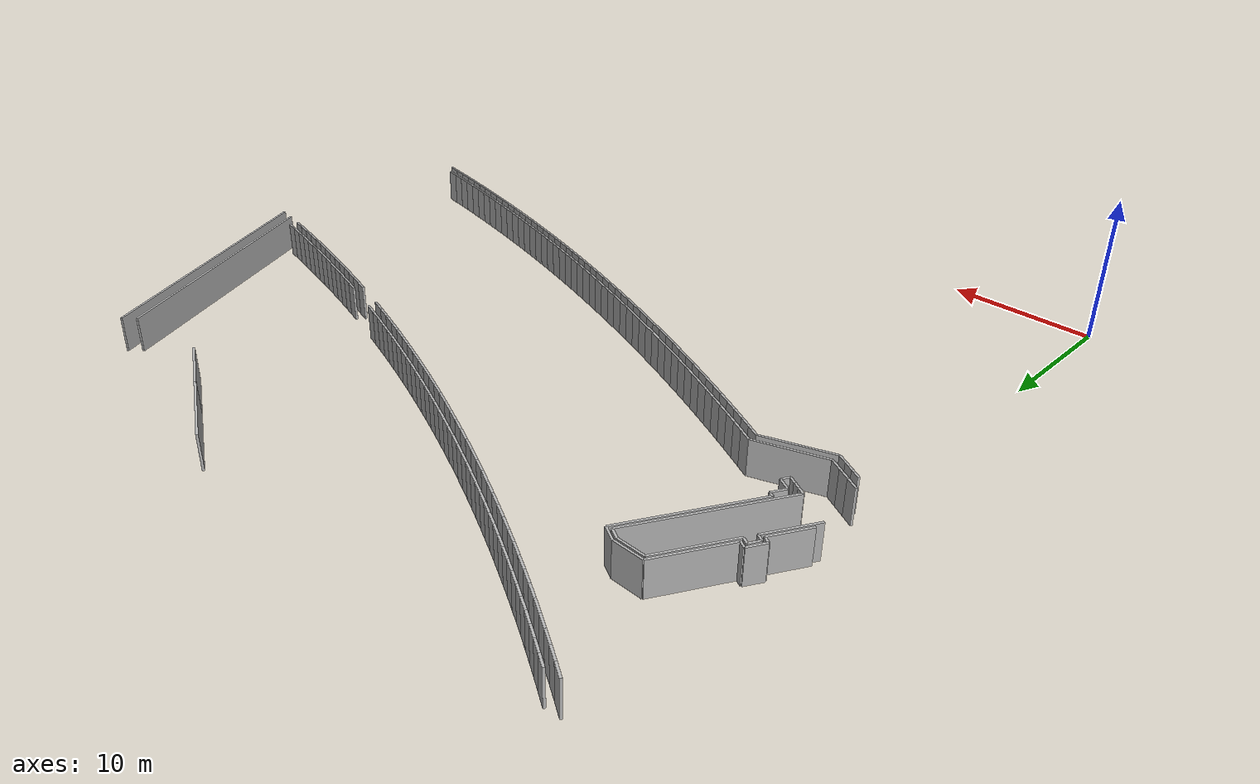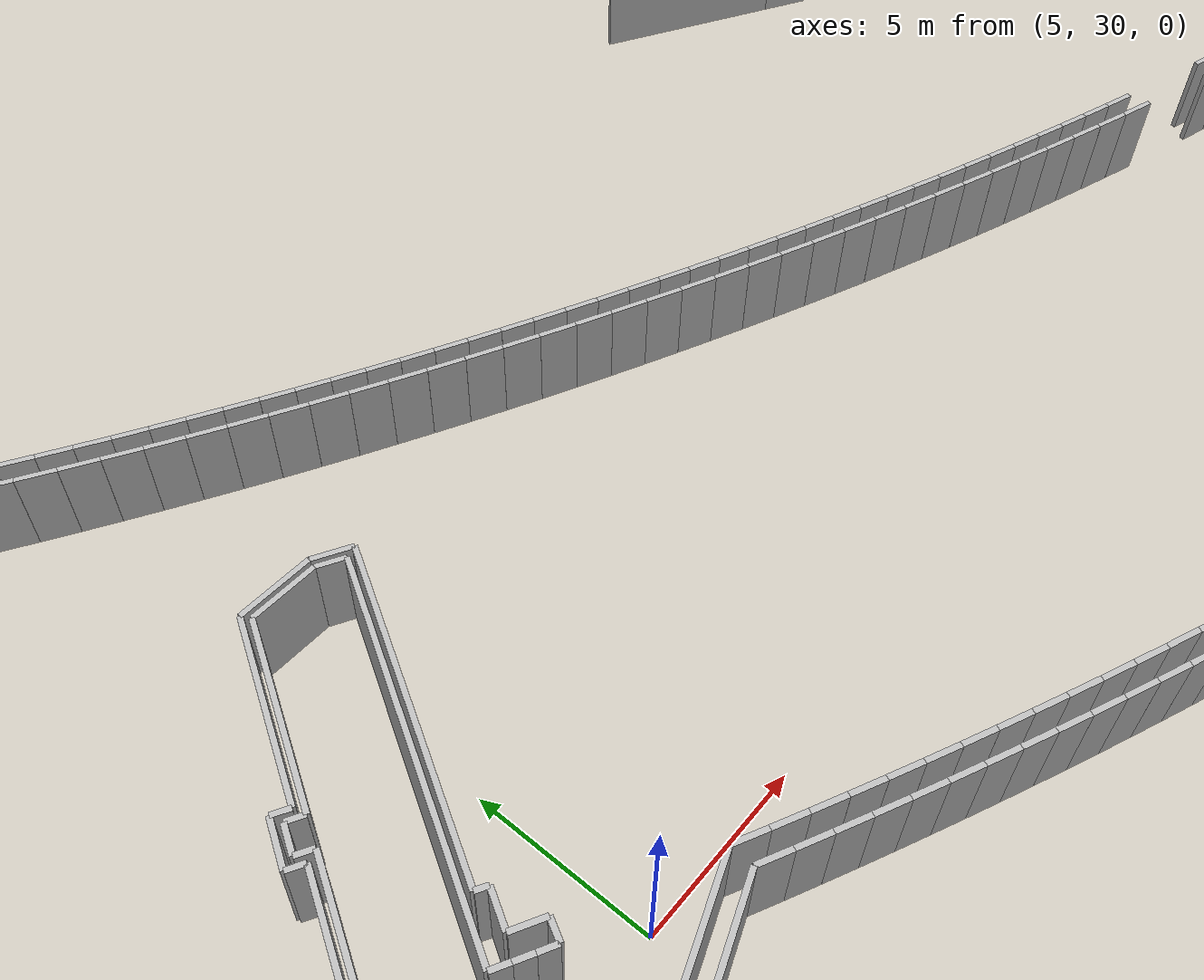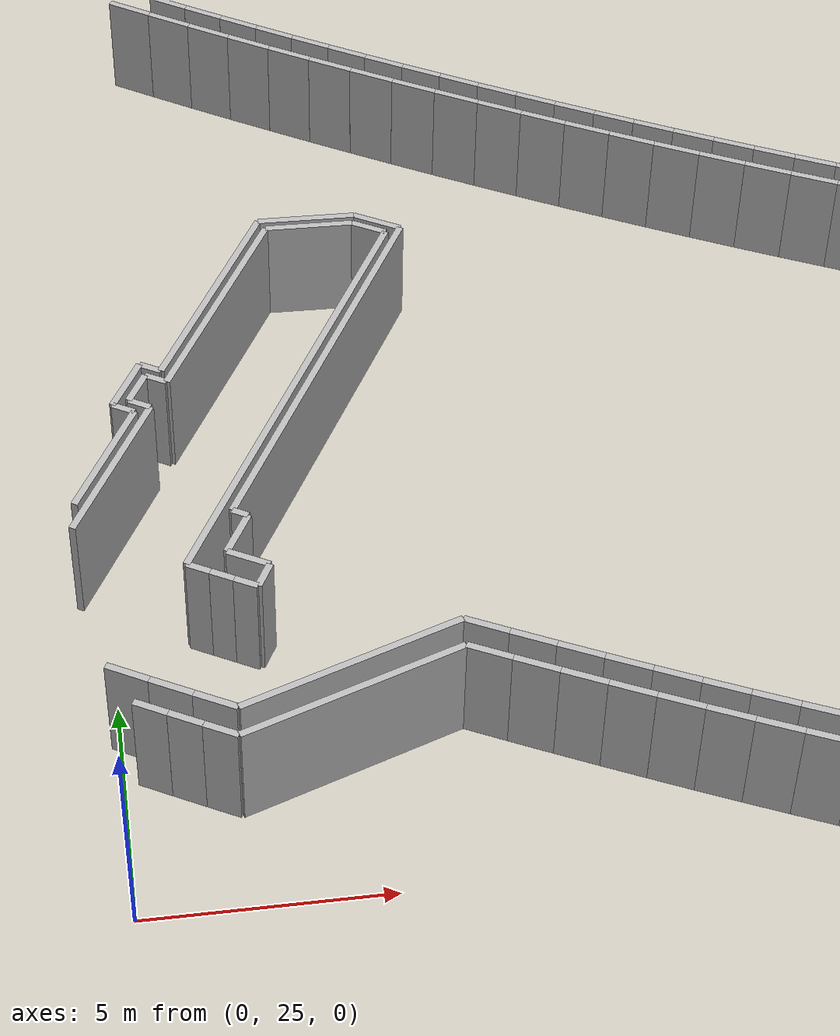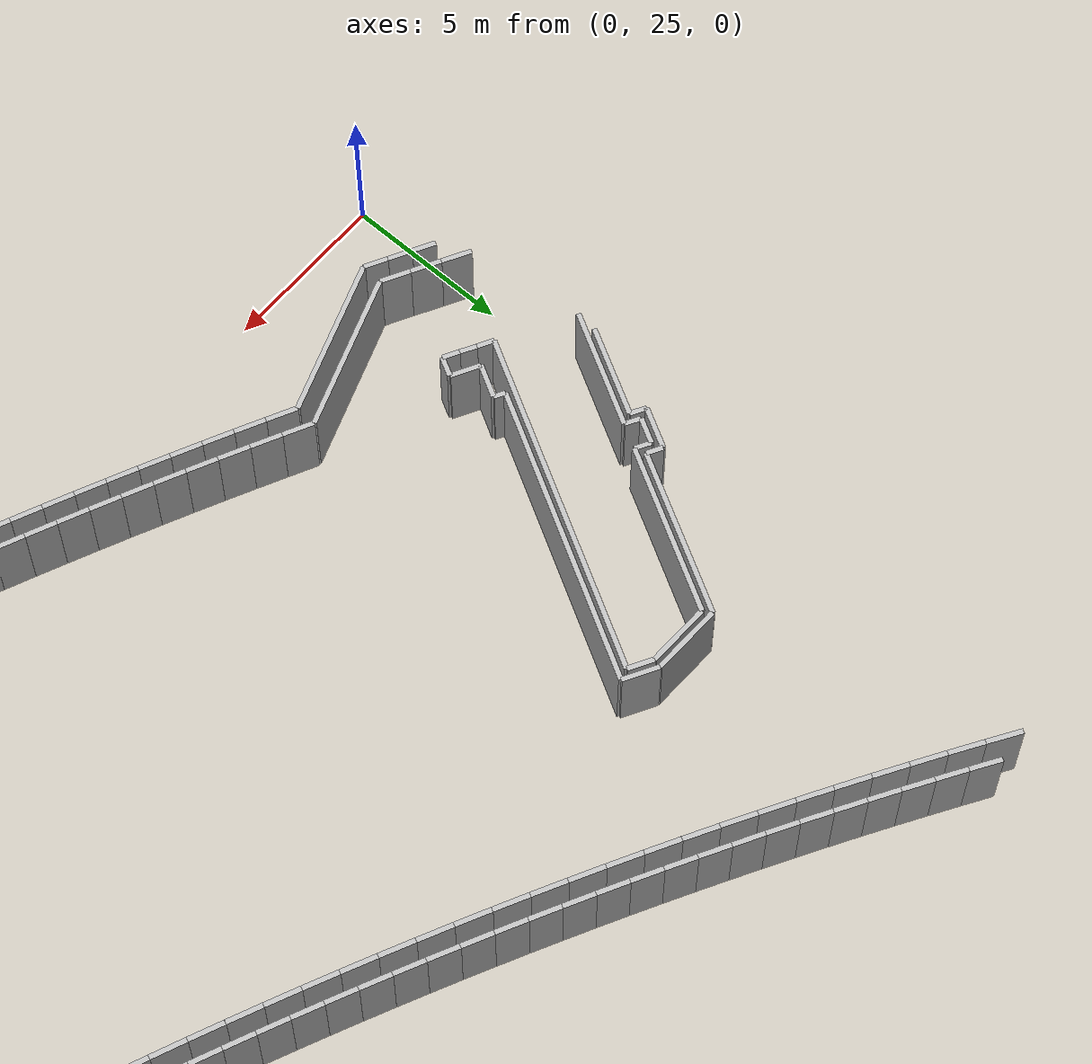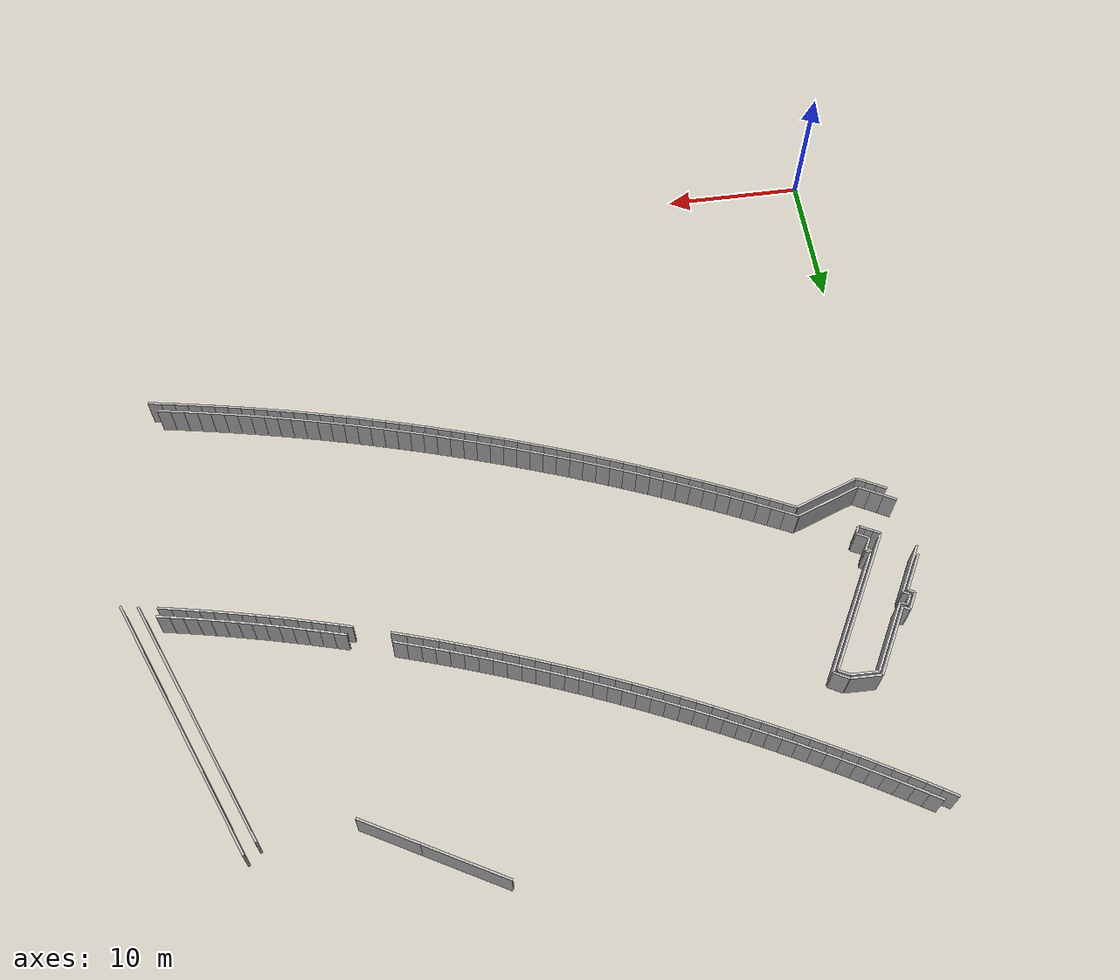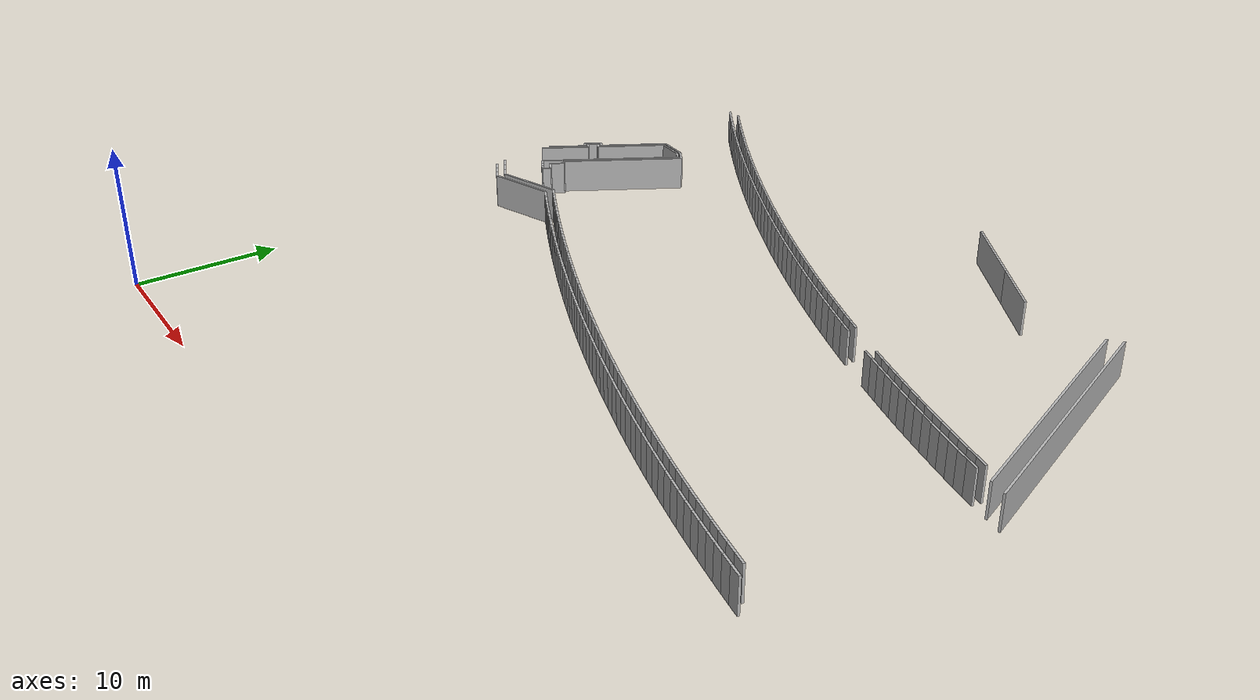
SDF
<?xml version="1.0" ?>
<sdf version="1.6">
  <model name="sps_0300">
    <pose frame="">0 0 0 0 -0 0</pose>
    <static>1</static>
    <self_collide>0</self_collide>
    <allow_auto_disable>0</allow_auto_disable>
    <link name="Wall42">
      <kinematic>0</kinematic>
      <gravity>1</gravity>
      <self_collide>0</self_collide>
      <collision name="collision">
        <geometry>
          <box>
            <size>3.66476 0.15 2.5</size>
          </box>
        </geometry>
        <pose frame="">0 0 0 0 -0 0</pose>
      </collision>
      <visual name="visual">
        <geometry>
          <box>
            <size>3.66476 0.15 2.5</size>
          </box>
        </geometry>
        <pose frame="">0 0 0 0 -0 0</pose>
        <cast_shadows>1</cast_shadows>
        <transparency>0.0</transparency>
      </visual>
      <pose frame="">0.297355 34.3015 1.25 0 0 -2.08078</pose>
    </link>
    <link name="Wall45">
      <kinematic>0</kinematic>
      <gravity>1</gravity>
      <self_collide>0</self_collide>
      <collision name="collision">
        <geometry>
          <box>
            <size>1.92312 0.15 2.5</size>
          </box>
        </geometry>
        <pose frame="">0 0 0 0 -0 0</pose>
      </collision>
      <visual name="visual">
        <geometry>
          <box>
            <size>1.92312 0.15 2.5</size>
          </box>
        </geometry>
        <pose frame="">0 0 0 0 -0 0</pose>
        <cast_shadows>1</cast_shadows>
        <transparency>0.0</transparency>
      </visual>
      <pose frame="">5.08193 41.115 1.25 0 -0 3.11861</pose>
    </link>
    <link name="Wall55">
      <kinematic>0</kinematic>
      <gravity>1</gravity>
      <self_collide>0</self_collide>
      <collision name="collision">
        <geometry>
          <box>
            <size>6.00747 0.15 2.5</size>
          </box>
        </geometry>
        <pose frame="">0 0 0 0 -0 0</pose>
      </collision>
      <visual name="visual">
        <geometry>
          <box>
            <size>6.00747 0.15 2.5</size>
          </box>
        </geometry>
        <pose frame="">0 0 0 0 -0 0</pose>
        <cast_shadows>1</cast_shadows>
        <transparency>0.0</transparency>
      </visual>
      <pose frame="">31.8468 49.6369 1.25 0 0 -0.50919</pose>
    </link>
    <link name="Wall56">
      <kinematic>0</kinematic>
      <gravity>1</gravity>
      <self_collide>0</self_collide>
      <collision name="collision">
        <geometry>
          <box>
            <size>4.34434 0.15 2.5</size>
          </box>
        </geometry>
        <pose frame="">0 0 0 0 -0 0</pose>
      </collision>
      <visual name="visual">
        <geometry>
          <box>
            <size>4.34434 0.15 2.5</size>
          </box>
        </geometry>
        <pose frame="">0 0 0 0 -0 0</pose>
        <cast_shadows>1</cast_shadows>
        <transparency>0.0</transparency>
      </visual>
      <pose frame="">36.3661 47.1138 1.25 0 0 -0.509191</pose>
    </link>
    <link name="Wall428">
      <kinematic>0</kinematic>
      <gravity>1</gravity>
      <self_collide>0</self_collide>
      <collision name="collision">
        <geometry>
          <box>
            <size>0.500592 0.15 2.5</size>
          </box>
        </geometry>
        <pose frame="">0 0 0 0 -0 0</pose>
      </collision>
      <visual name="visual">
        <geometry>
          <box>
            <size>0.500592 0.15 2.5</size>
          </box>
        </geometry>
        <pose frame="">0 0 0 0 -0 0</pose>
        <cast_shadows>1</cast_shadows>
        <transparency>0.0</transparency>
      </visual>
      <pose frame="">0.63375 35.9267 1.25 0 -0 2.6306</pose>
    </link>
    <link name="Wall1173">
      <kinematic>0</kinematic>
      <gravity>1</gravity>
      <self_collide>0</self_collide>
      <collision name="collision">
        <geometry>
          <box>
            <size>1.29954 0.15 2.5</size>
          </box>
        </geometry>
        <pose frame="">0 0 0 0 -0 0</pose>
      </collision>
      <visual name="visual">
        <geometry>
          <box>
            <size>1.29954 0.15 2.5</size>
          </box>
        </geometry>
        <pose frame="">0 0 0 0 -0 0</pose>
        <cast_shadows>1</cast_shadows>
        <transparency>0.0</transparency>
      </visual>
      <pose frame="">0.732749 36.6161 1.25 0 -0 1.06059</pose>
    </link>
    <link name="Wall1175">
      <kinematic>0</kinematic>
      <gravity>1</gravity>
      <self_collide>0</self_collide>
      <collision name="collision">
        <geometry>
          <box>
            <size>10.5653 0.15 2.5</size>
          </box>
        </geometry>
        <pose frame="">0 0 0 0 -0 0</pose>
      </collision>
      <visual name="visual">
        <geometry>
          <box>
            <size>10.5653 0.15 2.5</size>
          </box>
        </geometry>
        <pose frame="">0 0 0 0 -0 0</pose>
        <cast_shadows>1</cast_shadows>
        <transparency>0.0</transparency>
      </visual>
      <pose frame="">4.16296 36.092 1.25 0 -0 1.06083</pose>
    </link>
    <link name="Wall1176">
      <kinematic>0</kinematic>
      <gravity>1</gravity>
      <self_collide>0</self_collide>
      <collision name="collision">
        <geometry>
          <box>
            <size>9.165 0.15 2.5</size>
          </box>
        </geometry>
        <pose frame="">0 0 0 0 -0 0</pose>
      </collision>
      <visual name="visual">
        <geometry>
          <box>
            <size>9.165 0.15 2.5</size>
          </box>
        </geometry>
        <pose frame="">0 0 0 0 -0 0</pose>
        <cast_shadows>1</cast_shadows>
        <transparency>0.0</transparency>
      </visual>
      <pose frame="">4.84545 36.7988 1.25 0 0 -2.08072</pose>
    </link>
    <link name="Wall1492">
      <kinematic>0</kinematic>
      <gravity>1</gravity>
      <self_collide>0</self_collide>
      <collision name="collision">
        <geometry>
          <box>
            <size>0.499388 0.15 2.5</size>
          </box>
        </geometry>
        <pose frame="">0 0 0 0 -0 0</pose>
      </collision>
      <visual name="visual">
        <geometry>
          <box>
            <size>0.499388 0.15 2.5</size>
          </box>
        </geometry>
        <pose frame="">0 0 0 0 -0 0</pose>
        <cast_shadows>1</cast_shadows>
        <transparency>0.0</transparency>
      </visual>
      <pose frame="">0.974052 36.0228 1.25 0 0 -0.510945</pose>
    </link>
    <link name="Wall1493">
      <kinematic>0</kinematic>
      <gravity>1</gravity>
      <self_collide>0</self_collide>
      <collision name="collision">
        <geometry>
          <box>
            <size>0.499388 0.15 2.5</size>
          </box>
        </geometry>
        <pose frame="">0 0 0 0 -0 0</pose>
      </collision>
      <visual name="visual">
        <geometry>
          <box>
            <size>0.499388 0.15 2.5</size>
          </box>
        </geometry>
        <pose frame="">0 0 0 0 -0 0</pose>
        <cast_shadows>1</cast_shadows>
        <transparency>0.0</transparency>
      </visual>
      <pose frame="">1.36443 36.7212 1.25 0 -0 2.63065</pose>
    </link>
    <link name="Wall1494">
      <kinematic>0</kinematic>
      <gravity>1</gravity>
      <self_collide>0</self_collide>
      <collision name="collision">
        <geometry>
          <box>
            <size>1.04331 0.15 2.5</size>
          </box>
        </geometry>
        <pose frame="">0 0 0 0 -0 0</pose>
      </collision>
      <visual name="visual">
        <geometry>
          <box>
            <size>1.04331 0.15 2.5</size>
          </box>
        </geometry>
        <pose frame="">0 0 0 0 -0 0</pose>
        <cast_shadows>1</cast_shadows>
        <transparency>0.0</transparency>
      </visual>
      <pose frame="">2.65905 32.1731 1.25 0 0 -2.08108</pose>
    </link>
    <link name="Wall1495">
      <kinematic>0</kinematic>
      <gravity>1</gravity>
      <self_collide>0</self_collide>
      <collision name="collision">
        <geometry>
          <box>
            <size>0.921108 0.15 2.5</size>
          </box>
        </geometry>
        <pose frame="">0 0 0 0 -0 0</pose>
      </collision>
      <visual name="visual">
        <geometry>
          <box>
            <size>0.921108 0.15 2.5</size>
          </box>
        </geometry>
        <pose frame="">0 0 0 0 -0 0</pose>
        <cast_shadows>1</cast_shadows>
        <transparency>0.0</transparency>
      </visual>
      <pose frame="">2.80935 31.4988 1.25 0 -0 2.64576</pose>
    </link>
    <link name="Wall1496">
      <kinematic>0</kinematic>
      <gravity>1</gravity>
      <self_collide>0</self_collide>
      <collision name="collision">
        <geometry>
          <box>
            <size>5.19972 0.15 2.5</size>
          </box>
        </geometry>
        <pose frame="">0 0 0 0 -0 0</pose>
      </collision>
      <visual name="visual">
        <geometry>
          <box>
            <size>5.19972 0.15 2.5</size>
          </box>
        </geometry>
        <pose frame="">0 0 0 0 -0 0</pose>
        <cast_shadows>1</cast_shadows>
        <transparency>0.0</transparency>
      </visual>
      <pose frame="">2.85143 38.8681 1.25 0 0 -2.0808</pose>
    </link>
    <link name="Wall1498">
      <kinematic>0</kinematic>
      <gravity>1</gravity>
      <self_collide>0</self_collide>
      <collision name="collision">
        <geometry>
          <box>
            <size>2.136 0.15 2.5</size>
          </box>
        </geometry>
        <pose frame="">0 0 0 0 -0 0</pose>
      </collision>
      <visual name="visual">
        <geometry>
          <box>
            <size>2.136 0.15 2.5</size>
          </box>
        </geometry>
        <pose frame="">0 0 0 0 -0 0</pose>
        <cast_shadows>1</cast_shadows>
        <transparency>0.0</transparency>
      </visual>
      <pose frame="">5.04375 41.3663 1.25 0 0 -0.0230331</pose>
    </link>
    <link name="Wall1499">
      <kinematic>0</kinematic>
      <gravity>1</gravity>
      <self_collide>0</self_collide>
      <collision name="collision">
        <geometry>
          <box>
            <size>1.1125 0.15 2.5</size>
          </box>
        </geometry>
        <pose frame="">0 0 0 0 -0 0</pose>
      </collision>
      <visual name="visual">
        <geometry>
          <box>
            <size>1.1125 0.15 2.5</size>
          </box>
        </geometry>
        <pose frame="">0 0 0 0 -0 0</pose>
        <cast_shadows>1</cast_shadows>
        <transparency>0.0</transparency>
      </visual>
      <pose frame="">6.59685 41.07 1.25 0 0 -0.510306</pose>
    </link>
    <link name="Wall1788">
      <kinematic>0</kinematic>
      <gravity>1</gravity>
      <self_collide>0</self_collide>
      <collision name="collision">
        <geometry>
          <box>
            <size>0.800069 0.15 2.5</size>
          </box>
        </geometry>
        <pose frame="">0 0 0 0 -0 0</pose>
      </collision>
      <visual name="visual">
        <geometry>
          <box>
            <size>0.800069 0.15 2.5</size>
          </box>
        </geometry>
        <pose frame="">0 0 0 0 -0 0</pose>
        <cast_shadows>1</cast_shadows>
        <transparency>0.0</transparency>
      </visual>
      <pose frame="">0.951438 36.4941 1.25 0 0 -2.08052</pose>
    </link>
    <link name="Wall1789">
      <kinematic>0</kinematic>
      <gravity>1</gravity>
      <self_collide>0</self_collide>
      <collision name="collision">
        <geometry>
          <box>
            <size>0.499548 0.15 2.5</size>
          </box>
        </geometry>
        <pose frame="">0 0 0 0 -0 0</pose>
      </collision>
      <visual name="visual">
        <geometry>
          <box>
            <size>0.499548 0.15 2.5</size>
          </box>
        </geometry>
        <pose frame="">0 0 0 0 -0 0</pose>
        <cast_shadows>1</cast_shadows>
        <transparency>0.0</transparency>
      </visual>
      <pose frame="">1.26797 37.061 1.25 0 0 -0.510765</pose>
    </link>
    <link name="Wall1790">
      <kinematic>0</kinematic>
      <gravity>1</gravity>
      <self_collide>0</self_collide>
      <collision name="collision">
        <geometry>
          <box>
            <size>0.600244 0.15 2.5</size>
          </box>
        </geometry>
        <pose frame="">0 0 0 0 -0 0</pose>
      </collision>
      <visual name="visual">
        <geometry>
          <box>
            <size>0.600244 0.15 2.5</size>
          </box>
        </geometry>
        <pose frame="">0 0 0 0 -0 0</pose>
        <cast_shadows>1</cast_shadows>
        <transparency>0.0</transparency>
      </visual>
      <pose frame="">3.07244 31.0153 1.25 0 0 -2.06364</pose>
    </link>
    <link name="Wall1791">
      <kinematic>0</kinematic>
      <gravity>1</gravity>
      <self_collide>0</self_collide>
      <collision name="collision">
        <geometry>
          <box>
            <size>5.10107 0.15 2.5</size>
          </box>
        </geometry>
        <pose frame="">0 0 0 0 -0 0</pose>
      </collision>
      <visual name="visual">
        <geometry>
          <box>
            <size>5.10107 0.15 2.5</size>
          </box>
        </geometry>
        <pose frame="">0 0 0 0 -0 0</pose>
        <cast_shadows>1</cast_shadows>
        <transparency>0.0</transparency>
      </visual>
      <pose frame="">2.73095 39.1649 1.25 0 -0 1.06081</pose>
    </link>
    <link name="Wall1792">
      <kinematic>0</kinematic>
      <gravity>1</gravity>
      <self_collide>0</self_collide>
      <collision name="collision">
        <geometry>
          <box>
            <size>4.78681 0.15 2.5</size>
          </box>
        </geometry>
        <pose frame="">0 0 0 0 -0 0</pose>
      </collision>
      <visual name="visual">
        <geometry>
          <box>
            <size>4.78681 0.15 2.5</size>
          </box>
        </geometry>
        <pose frame="">0 0 0 0 -0 0</pose>
        <cast_shadows>1</cast_shadows>
        <transparency>0.0</transparency>
      </visual>
      <pose frame="">4.47057 27.9739 1.25 0 0 -2.79724</pose>
    </link>
    <link name="Wall1793">
      <kinematic>0</kinematic>
      <gravity>1</gravity>
      <self_collide>0</self_collide>
      <collision name="collision">
        <geometry>
          <box>
            <size>4.78058 0.15 2.5</size>
          </box>
        </geometry>
        <pose frame="">0 0 0 0 -0 0</pose>
      </collision>
      <visual name="visual">
        <geometry>
          <box>
            <size>4.78058 0.15 2.5</size>
          </box>
        </geometry>
        <pose frame="">0 0 0 0 -0 0</pose>
        <cast_shadows>1</cast_shadows>
        <transparency>0.0</transparency>
      </visual>
      <pose frame="">4.51397 28.6268 1.25 0 0 -2.79717</pose>
    </link>
    <link name="Wall2132">
      <kinematic>0</kinematic>
      <gravity>1</gravity>
      <self_collide>0</self_collide>
      <collision name="collision">
        <geometry>
          <box>
            <size>2.81236 0.15 2.5</size>
          </box>
        </geometry>
        <pose frame="">0 0 0 0 -0 0</pose>
      </collision>
      <visual name="visual">
        <geometry>
          <box>
            <size>2.81236 0.15 2.5</size>
          </box>
        </geometry>
        <pose frame="">0 0 0 0 -0 0</pose>
        <cast_shadows>1</cast_shadows>
        <transparency>0.0</transparency>
      </visual>
      <pose frame="">0.16555 34.5771 1.25 0 -0 1.06075</pose>
    </link>
    <link name="Wall2515">
      <kinematic>0</kinematic>
      <gravity>1</gravity>
      <self_collide>0</self_collide>
      <collision name="collision">
        <geometry>
          <box>
            <size>0.349799 0.15 2.5</size>
          </box>
        </geometry>
        <pose frame="">0 0 0 0 -0 0</pose>
      </collision>
      <visual name="visual">
        <geometry>
          <box>
            <size>0.349799 0.15 2.5</size>
          </box>
        </geometry>
        <pose frame="">0 0 0 0 -0 0</pose>
        <cast_shadows>1</cast_shadows>
        <transparency>0.0</transparency>
      </visual>
      <pose frame="">2.76125 32.7138 1.25 0 0 -0.510641</pose>
    </link>
    <link name="Wall2517">
      <kinematic>0</kinematic>
      <gravity>1</gravity>
      <self_collide>0</self_collide>
      <collision name="collision">
        <geometry>
          <box>
            <size>0.800152 0.15 2.5</size>
          </box>
        </geometry>
        <pose frame="">0 0 0 0 -0 0</pose>
      </collision>
      <visual name="visual">
        <geometry>
          <box>
            <size>0.800152 0.15 2.5</size>
          </box>
        </geometry>
        <pose frame="">0 0 0 0 -0 0</pose>
        <cast_shadows>1</cast_shadows>
        <transparency>0.0</transparency>
      </visual>
      <pose frame="">6.39245 40.8977 1.25 0 -0 2.63184</pose>
    </link>
    <link name="Wall9144">
      <kinematic>0</kinematic>
      <gravity>1</gravity>
      <self_collide>0</self_collide>
      <collision name="collision">
        <geometry>
          <box>
            <size>0.950719 0.15 2.5</size>
          </box>
        </geometry>
        <pose frame="">0 0 0 0 -0 0</pose>
      </collision>
      <visual name="visual">
        <geometry>
          <box>
            <size>0.950719 0.15 2.5</size>
          </box>
        </geometry>
        <pose frame="">0 0 0 0 -0 0</pose>
        <cast_shadows>1</cast_shadows>
        <transparency>0.0</transparency>
      </visual>
      <pose frame="">2.61306 49.6466 1.25 0 0 -0.557497</pose>
    </link>
    <link name="Wall9145">
      <kinematic>0</kinematic>
      <gravity>1</gravity>
      <self_collide>0</self_collide>
      <collision name="collision">
        <geometry>
          <box>
            <size>0.950723 0.15 2.5</size>
          </box>
        </geometry>
        <pose frame="">0 0 0 0 -0 0</pose>
      </collision>
      <visual name="visual">
        <geometry>
          <box>
            <size>0.950723 0.15 2.5</size>
          </box>
        </geometry>
        <pose frame="">0 0 0 0 -0 0</pose>
        <cast_shadows>1</cast_shadows>
        <transparency>0.0</transparency>
      </visual>
      <pose frame="">3.42156 49.1464 1.25 0 0 -0.550549</pose>
    </link>
    <link name="Wall9146">
      <kinematic>0</kinematic>
      <gravity>1</gravity>
      <self_collide>0</self_collide>
      <collision name="collision">
        <geometry>
          <box>
            <size>0.950921 0.15 2.5</size>
          </box>
        </geometry>
        <pose frame="">0 0 0 0 -0 0</pose>
      </collision>
      <visual name="visual">
        <geometry>
          <box>
            <size>0.950921 0.15 2.5</size>
          </box>
        </geometry>
        <pose frame="">0 0 0 0 -0 0</pose>
        <cast_shadows>1</cast_shadows>
        <transparency>0.0</transparency>
      </visual>
      <pose frame="">4.23348 48.6516 1.25 0 0 -0.544107</pose>
    </link>
    <link name="Wall9147">
      <kinematic>0</kinematic>
      <gravity>1</gravity>
      <self_collide>0</self_collide>
      <collision name="collision">
        <geometry>
          <box>
            <size>0.950721 0.15 2.5</size>
          </box>
        </geometry>
        <pose frame="">0 0 0 0 -0 0</pose>
      </collision>
      <visual name="visual">
        <geometry>
          <box>
            <size>0.950721 0.15 2.5</size>
          </box>
        </geometry>
        <pose frame="">0 0 0 0 -0 0</pose>
        <cast_shadows>1</cast_shadows>
        <transparency>0.0</transparency>
      </visual>
      <pose frame="">5.04867 48.1622 1.25 0 0 -0.537271</pose>
    </link>
    <link name="Wall9148">
      <kinematic>0</kinematic>
      <gravity>1</gravity>
      <self_collide>0</self_collide>
      <collision name="collision">
        <geometry>
          <box>
            <size>0.950929 0.15 2.5</size>
          </box>
        </geometry>
        <pose frame="">0 0 0 0 -0 0</pose>
      </collision>
      <visual name="visual">
        <geometry>
          <box>
            <size>0.950929 0.15 2.5</size>
          </box>
        </geometry>
        <pose frame="">0 0 0 0 -0 0</pose>
        <cast_shadows>1</cast_shadows>
        <transparency>0.0</transparency>
      </visual>
      <pose frame="">5.86715 47.6783 1.25 0 0 -0.530579</pose>
    </link>
    <link name="Wall9149">
      <kinematic>0</kinematic>
      <gravity>1</gravity>
      <self_collide>0</self_collide>
      <collision name="collision">
        <geometry>
          <box>
            <size>0.950742 0.15 2.5</size>
          </box>
        </geometry>
        <pose frame="">0 0 0 0 -0 0</pose>
      </collision>
      <visual name="visual">
        <geometry>
          <box>
            <size>0.950742 0.15 2.5</size>
          </box>
        </geometry>
        <pose frame="">0 0 0 0 -0 0</pose>
        <cast_shadows>1</cast_shadows>
        <transparency>0.0</transparency>
      </visual>
      <pose frame="">6.68886 47.1999 1.25 0 0 -0.52386</pose>
    </link>
    <link name="Wall9150">
      <kinematic>0</kinematic>
      <gravity>1</gravity>
      <self_collide>0</self_collide>
      <collision name="collision">
        <geometry>
          <box>
            <size>0.95068 0.15 2.5</size>
          </box>
        </geometry>
        <pose frame="">0 0 0 0 -0 0</pose>
      </collision>
      <visual name="visual">
        <geometry>
          <box>
            <size>0.95068 0.15 2.5</size>
          </box>
        </geometry>
        <pose frame="">0 0 0 0 -0 0</pose>
        <cast_shadows>1</cast_shadows>
        <transparency>0.0</transparency>
      </visual>
      <pose frame="">7.51366 46.7271 1.25 0 0 -0.517163</pose>
    </link>
    <link name="Wall9151">
      <kinematic>0</kinematic>
      <gravity>1</gravity>
      <self_collide>0</self_collide>
      <collision name="collision">
        <geometry>
          <box>
            <size>0.95104 0.15 2.5</size>
          </box>
        </geometry>
        <pose frame="">0 0 0 0 -0 0</pose>
      </collision>
      <visual name="visual">
        <geometry>
          <box>
            <size>0.95104 0.15 2.5</size>
          </box>
        </geometry>
        <pose frame="">0 0 0 0 -0 0</pose>
        <cast_shadows>1</cast_shadows>
        <transparency>0.0</transparency>
      </visual>
      <pose frame="">8.34176 46.2598 1.25 0 0 -0.51039</pose>
    </link>
    <link name="Wall9152">
      <kinematic>0</kinematic>
      <gravity>1</gravity>
      <self_collide>0</self_collide>
      <collision name="collision">
        <geometry>
          <box>
            <size>0.950714 0.15 2.5</size>
          </box>
        </geometry>
        <pose frame="">0 0 0 0 -0 0</pose>
      </collision>
      <visual name="visual">
        <geometry>
          <box>
            <size>0.950714 0.15 2.5</size>
          </box>
        </geometry>
        <pose frame="">0 0 0 0 -0 0</pose>
        <cast_shadows>1</cast_shadows>
        <transparency>0.0</transparency>
      </visual>
      <pose frame="">9.17297 45.798 1.25 0 0 -0.503825</pose>
    </link>
    <link name="Wall9153">
      <kinematic>0</kinematic>
      <gravity>1</gravity>
      <self_collide>0</self_collide>
      <collision name="collision">
        <geometry>
          <box>
            <size>0.950887 0.15 2.5</size>
          </box>
        </geometry>
        <pose frame="">0 0 0 0 -0 0</pose>
      </collision>
      <visual name="visual">
        <geometry>
          <box>
            <size>0.950887 0.15 2.5</size>
          </box>
        </geometry>
        <pose frame="">0 0 0 0 -0 0</pose>
        <cast_shadows>1</cast_shadows>
        <transparency>0.0</transparency>
      </visual>
      <pose frame="">10.0072 45.3418 1.25 0 0 -0.497067</pose>
    </link>
    <link name="Wall9154">
      <kinematic>0</kinematic>
      <gravity>1</gravity>
      <self_collide>0</self_collide>
      <collision name="collision">
        <geometry>
          <box>
            <size>0.950615 0.15 2.5</size>
          </box>
        </geometry>
        <pose frame="">0 0 0 0 -0 0</pose>
      </collision>
      <visual name="visual">
        <geometry>
          <box>
            <size>0.950615 0.15 2.5</size>
          </box>
        </geometry>
        <pose frame="">0 0 0 0 -0 0</pose>
        <cast_shadows>1</cast_shadows>
        <transparency>0.0</transparency>
      </visual>
      <pose frame="">10.8444 44.8912 1.25 0 0 -0.490441</pose>
    </link>
    <link name="Wall9155">
      <kinematic>0</kinematic>
      <gravity>1</gravity>
      <self_collide>0</self_collide>
      <collision name="collision">
        <geometry>
          <box>
            <size>0.950875 0.15 2.5</size>
          </box>
        </geometry>
        <pose frame="">0 0 0 0 -0 0</pose>
      </collision>
      <visual name="visual">
        <geometry>
          <box>
            <size>0.950875 0.15 2.5</size>
          </box>
        </geometry>
        <pose frame="">0 0 0 0 -0 0</pose>
        <cast_shadows>1</cast_shadows>
        <transparency>0.0</transparency>
      </visual>
      <pose frame="">11.6845 44.4462 1.25 0 0 -0.483686</pose>
    </link>
    <link name="Wall9156">
      <kinematic>0</kinematic>
      <gravity>1</gravity>
      <self_collide>0</self_collide>
      <collision name="collision">
        <geometry>
          <box>
            <size>0.950902 0.15 2.5</size>
          </box>
        </geometry>
        <pose frame="">0 0 0 0 -0 0</pose>
      </collision>
      <visual name="visual">
        <geometry>
          <box>
            <size>0.950902 0.15 2.5</size>
          </box>
        </geometry>
        <pose frame="">0 0 0 0 -0 0</pose>
        <cast_shadows>1</cast_shadows>
        <transparency>0.0</transparency>
      </visual>
      <pose frame="">12.5279 44.0069 1.25 0 0 -0.476795</pose>
    </link>
    <link name="Wall9157">
      <kinematic>0</kinematic>
      <gravity>1</gravity>
      <self_collide>0</self_collide>
      <collision name="collision">
        <geometry>
          <box>
            <size>0.950814 0.15 2.5</size>
          </box>
        </geometry>
        <pose frame="">0 0 0 0 -0 0</pose>
      </collision>
      <visual name="visual">
        <geometry>
          <box>
            <size>0.950814 0.15 2.5</size>
          </box>
        </geometry>
        <pose frame="">0 0 0 0 -0 0</pose>
        <cast_shadows>1</cast_shadows>
        <transparency>0.0</transparency>
      </visual>
      <pose frame="">13.3741 43.5733 1.25 0 0 -0.470279</pose>
    </link>
    <link name="Wall9158">
      <kinematic>0</kinematic>
      <gravity>1</gravity>
      <self_collide>0</self_collide>
      <collision name="collision">
        <geometry>
          <box>
            <size>0.950848 0.15 2.5</size>
          </box>
        </geometry>
        <pose frame="">0 0 0 0 -0 0</pose>
      </collision>
      <visual name="visual">
        <geometry>
          <box>
            <size>0.950848 0.15 2.5</size>
          </box>
        </geometry>
        <pose frame="">0 0 0 0 -0 0</pose>
        <cast_shadows>1</cast_shadows>
        <transparency>0.0</transparency>
      </visual>
      <pose frame="">14.2232 43.1454 1.25 0 0 -0.463361</pose>
    </link>
    <link name="Wall9159">
      <kinematic>0</kinematic>
      <gravity>1</gravity>
      <self_collide>0</self_collide>
      <collision name="collision">
        <geometry>
          <box>
            <size>0.950706 0.15 2.5</size>
          </box>
        </geometry>
        <pose frame="">0 0 0 0 -0 0</pose>
      </collision>
      <visual name="visual">
        <geometry>
          <box>
            <size>0.950706 0.15 2.5</size>
          </box>
        </geometry>
        <pose frame="">0 0 0 0 -0 0</pose>
        <cast_shadows>1</cast_shadows>
        <transparency>0.0</transparency>
      </visual>
      <pose frame="">15.0751 42.7232 1.25 0 0 -0.456843</pose>
    </link>
    <link name="Wall9160">
      <kinematic>0</kinematic>
      <gravity>1</gravity>
      <self_collide>0</self_collide>
      <collision name="collision">
        <geometry>
          <box>
            <size>0.950741 0.15 2.5</size>
          </box>
        </geometry>
        <pose frame="">0 0 0 0 -0 0</pose>
      </collision>
      <visual name="visual">
        <geometry>
          <box>
            <size>0.950741 0.15 2.5</size>
          </box>
        </geometry>
        <pose frame="">0 0 0 0 -0 0</pose>
        <cast_shadows>1</cast_shadows>
        <transparency>0.0</transparency>
      </visual>
      <pose frame="">15.9296 42.3066 1.25 0 0 -0.450326</pose>
    </link>
    <link name="Wall9161">
      <kinematic>0</kinematic>
      <gravity>1</gravity>
      <self_collide>0</self_collide>
      <collision name="collision">
        <geometry>
          <box>
            <size>0.950987 0.15 2.5</size>
          </box>
        </geometry>
        <pose frame="">0 0 0 0 -0 0</pose>
      </collision>
      <visual name="visual">
        <geometry>
          <box>
            <size>0.950987 0.15 2.5</size>
          </box>
        </geometry>
        <pose frame="">0 0 0 0 -0 0</pose>
        <cast_shadows>1</cast_shadows>
        <transparency>0.0</transparency>
      </visual>
      <pose frame="">16.7871 41.8957 1.25 0 0 -0.44344</pose>
    </link>
    <link name="Wall9162">
      <kinematic>0</kinematic>
      <gravity>1</gravity>
      <self_collide>0</self_collide>
      <collision name="collision">
        <geometry>
          <box>
            <size>0.950865 0.15 2.5</size>
          </box>
        </geometry>
        <pose frame="">0 0 0 0 -0 0</pose>
      </collision>
      <visual name="visual">
        <geometry>
          <box>
            <size>0.950865 0.15 2.5</size>
          </box>
        </geometry>
        <pose frame="">0 0 0 0 -0 0</pose>
        <cast_shadows>1</cast_shadows>
        <transparency>0.0</transparency>
      </visual>
      <pose frame="">17.6475 41.4906 1.25 0 0 -0.436689</pose>
    </link>
    <link name="Wall9163">
      <kinematic>0</kinematic>
      <gravity>1</gravity>
      <self_collide>0</self_collide>
      <collision name="collision">
        <geometry>
          <box>
            <size>0.950783 0.15 2.5</size>
          </box>
        </geometry>
        <pose frame="">0 0 0 0 -0 0</pose>
      </collision>
      <visual name="visual">
        <geometry>
          <box>
            <size>0.950783 0.15 2.5</size>
          </box>
        </geometry>
        <pose frame="">0 0 0 0 -0 0</pose>
        <cast_shadows>1</cast_shadows>
        <transparency>0.0</transparency>
      </visual>
      <pose frame="">18.5104 41.0913 1.25 0 0 -0.430081</pose>
    </link>
    <link name="Wall9164">
      <kinematic>0</kinematic>
      <gravity>1</gravity>
      <self_collide>0</self_collide>
      <collision name="collision">
        <geometry>
          <box>
            <size>0.950914 0.15 2.5</size>
          </box>
        </geometry>
        <pose frame="">0 0 0 0 -0 0</pose>
      </collision>
      <visual name="visual">
        <geometry>
          <box>
            <size>0.950914 0.15 2.5</size>
          </box>
        </geometry>
        <pose frame="">0 0 0 0 -0 0</pose>
        <cast_shadows>1</cast_shadows>
        <transparency>0.0</transparency>
      </visual>
      <pose frame="">19.376 40.6978 1.25 0 0 -0.423249</pose>
    </link>
    <link name="Wall9165">
      <kinematic>0</kinematic>
      <gravity>1</gravity>
      <self_collide>0</self_collide>
      <collision name="collision">
        <geometry>
          <box>
            <size>0.950674 0.15 2.5</size>
          </box>
        </geometry>
        <pose frame="">0 0 0 0 -0 0</pose>
      </collision>
      <visual name="visual">
        <geometry>
          <box>
            <size>0.950674 0.15 2.5</size>
          </box>
        </geometry>
        <pose frame="">0 0 0 0 -0 0</pose>
        <cast_shadows>1</cast_shadows>
        <transparency>0.0</transparency>
      </visual>
      <pose frame="">20.2442 40.3102 1.25 0 0 -0.416542</pose>
    </link>
    <link name="Wall9166">
      <kinematic>0</kinematic>
      <gravity>1</gravity>
      <self_collide>0</self_collide>
      <collision name="collision">
        <geometry>
          <box>
            <size>0.950798 0.15 2.5</size>
          </box>
        </geometry>
        <pose frame="">0 0 0 0 -0 0</pose>
      </collision>
      <visual name="visual">
        <geometry>
          <box>
            <size>0.950798 0.15 2.5</size>
          </box>
        </geometry>
        <pose frame="">0 0 0 0 -0 0</pose>
        <cast_shadows>1</cast_shadows>
        <transparency>0.0</transparency>
      </visual>
      <pose frame="">21.1149 39.9284 1.25 0 0 -0.409966</pose>
    </link>
    <link name="Wall9167">
      <kinematic>0</kinematic>
      <gravity>1</gravity>
      <self_collide>0</self_collide>
      <collision name="collision">
        <geometry>
          <box>
            <size>0.950787 0.15 2.5</size>
          </box>
        </geometry>
        <pose frame="">0 0 0 0 -0 0</pose>
      </collision>
      <visual name="visual">
        <geometry>
          <box>
            <size>0.950787 0.15 2.5</size>
          </box>
        </geometry>
        <pose frame="">0 0 0 0 -0 0</pose>
        <cast_shadows>1</cast_shadows>
        <transparency>0.0</transparency>
      </visual>
      <pose frame="">21.9882 39.5524 1.25 0 0 -0.403122</pose>
    </link>
    <link name="Wall9168">
      <kinematic>0</kinematic>
      <gravity>1</gravity>
      <self_collide>0</self_collide>
      <collision name="collision">
        <geometry>
          <box>
            <size>0.950802 0.15 2.5</size>
          </box>
        </geometry>
        <pose frame="">0 0 0 0 -0 0</pose>
      </collision>
      <visual name="visual">
        <geometry>
          <box>
            <size>0.950802 0.15 2.5</size>
          </box>
        </geometry>
        <pose frame="">0 0 0 0 -0 0</pose>
        <cast_shadows>1</cast_shadows>
        <transparency>0.0</transparency>
      </visual>
      <pose frame="">22.8639 39.1823 1.25 0 0 -0.396564</pose>
    </link>
    <link name="Wall9169">
      <kinematic>0</kinematic>
      <gravity>1</gravity>
      <self_collide>0</self_collide>
      <collision name="collision">
        <geometry>
          <box>
            <size>0.950856 0.15 2.5</size>
          </box>
        </geometry>
        <pose frame="">0 0 0 0 -0 0</pose>
      </collision>
      <visual name="visual">
        <geometry>
          <box>
            <size>0.950856 0.15 2.5</size>
          </box>
        </geometry>
        <pose frame="">0 0 0 0 -0 0</pose>
        <cast_shadows>1</cast_shadows>
        <transparency>0.0</transparency>
      </visual>
      <pose frame="">23.7422 38.8181 1.25 0 0 -0.389661</pose>
    </link>
    <link name="Wall9170">
      <kinematic>0</kinematic>
      <gravity>1</gravity>
      <self_collide>0</self_collide>
      <collision name="collision">
        <geometry>
          <box>
            <size>0.950831 0.15 2.5</size>
          </box>
        </geometry>
        <pose frame="">0 0 0 0 -0 0</pose>
      </collision>
      <visual name="visual">
        <geometry>
          <box>
            <size>0.950831 0.15 2.5</size>
          </box>
        </geometry>
        <pose frame="">0 0 0 0 -0 0</pose>
        <cast_shadows>1</cast_shadows>
        <transparency>0.0</transparency>
      </visual>
      <pose frame="">24.6229 38.4597 1.25 0 0 -0.383296</pose>
    </link>
    <link name="Wall9171">
      <kinematic>0</kinematic>
      <gravity>1</gravity>
      <self_collide>0</self_collide>
      <collision name="collision">
        <geometry>
          <box>
            <size>0.950734 0.15 2.5</size>
          </box>
        </geometry>
        <pose frame="">0 0 0 0 -0 0</pose>
      </collision>
      <visual name="visual">
        <geometry>
          <box>
            <size>0.950734 0.15 2.5</size>
          </box>
        </geometry>
        <pose frame="">0 0 0 0 -0 0</pose>
        <cast_shadows>1</cast_shadows>
        <transparency>0.0</transparency>
      </visual>
      <pose frame="">25.506 38.1072 1.25 0 0 -0.376286</pose>
    </link>
    <link name="Wall9172">
      <kinematic>0</kinematic>
      <gravity>1</gravity>
      <self_collide>0</self_collide>
      <collision name="collision">
        <geometry>
          <box>
            <size>0.950793 0.15 2.5</size>
          </box>
        </geometry>
        <pose frame="">0 0 0 0 -0 0</pose>
      </collision>
      <visual name="visual">
        <geometry>
          <box>
            <size>0.950793 0.15 2.5</size>
          </box>
        </geometry>
        <pose frame="">0 0 0 0 -0 0</pose>
        <cast_shadows>1</cast_shadows>
        <transparency>0.0</transparency>
      </visual>
      <pose frame="">26.3914 37.7608 1.25 0 0 -0.369575</pose>
    </link>
    <link name="Wall9173">
      <kinematic>0</kinematic>
      <gravity>1</gravity>
      <self_collide>0</self_collide>
      <collision name="collision">
        <geometry>
          <box>
            <size>0.950746 0.15 2.5</size>
          </box>
        </geometry>
        <pose frame="">0 0 0 0 -0 0</pose>
      </collision>
      <visual name="visual">
        <geometry>
          <box>
            <size>0.950746 0.15 2.5</size>
          </box>
        </geometry>
        <pose frame="">0 0 0 0 -0 0</pose>
        <cast_shadows>1</cast_shadows>
        <transparency>0.0</transparency>
      </visual>
      <pose frame="">27.2791 37.4203 1.25 0 0 -0.362993</pose>
    </link>
    <link name="Wall9174">
      <kinematic>0</kinematic>
      <gravity>1</gravity>
      <self_collide>0</self_collide>
      <collision name="collision">
        <geometry>
          <box>
            <size>0.950933 0.15 2.5</size>
          </box>
        </geometry>
        <pose frame="">0 0 0 0 -0 0</pose>
      </collision>
      <visual name="visual">
        <geometry>
          <box>
            <size>0.950933 0.15 2.5</size>
          </box>
        </geometry>
        <pose frame="">0 0 0 0 -0 0</pose>
        <cast_shadows>1</cast_shadows>
        <transparency>0.0</transparency>
      </visual>
      <pose frame="">28.1691 37.0856 1.25 0 0 -0.356404</pose>
    </link>
    <link name="Wall9175">
      <kinematic>0</kinematic>
      <gravity>1</gravity>
      <self_collide>0</self_collide>
      <collision name="collision">
        <geometry>
          <box>
            <size>0.950692 0.15 2.5</size>
          </box>
        </geometry>
        <pose frame="">0 0 0 0 -0 0</pose>
      </collision>
      <visual name="visual">
        <geometry>
          <box>
            <size>0.950692 0.15 2.5</size>
          </box>
        </geometry>
        <pose frame="">0 0 0 0 -0 0</pose>
        <cast_shadows>1</cast_shadows>
        <transparency>0.0</transparency>
      </visual>
      <pose frame="">29.0612 36.7569 1.25 0 0 -0.349588</pose>
    </link>
    <link name="Wall9176">
      <kinematic>0</kinematic>
      <gravity>1</gravity>
      <self_collide>0</self_collide>
      <collision name="collision">
        <geometry>
          <box>
            <size>0.950766 0.15 2.5</size>
          </box>
        </geometry>
        <pose frame="">0 0 0 0 -0 0</pose>
      </collision>
      <visual name="visual">
        <geometry>
          <box>
            <size>0.950766 0.15 2.5</size>
          </box>
        </geometry>
        <pose frame="">0 0 0 0 -0 0</pose>
        <cast_shadows>1</cast_shadows>
        <transparency>0.0</transparency>
      </visual>
      <pose frame="">29.9556 36.4343 1.25 0 0 -0.342804</pose>
    </link>
    <link name="Wall9177">
      <kinematic>0</kinematic>
      <gravity>1</gravity>
      <self_collide>0</self_collide>
      <collision name="collision">
        <geometry>
          <box>
            <size>0.950789 0.15 2.5</size>
          </box>
        </geometry>
        <pose frame="">0 0 0 0 -0 0</pose>
      </collision>
      <visual name="visual">
        <geometry>
          <box>
            <size>0.950789 0.15 2.5</size>
          </box>
        </geometry>
        <pose frame="">0 0 0 0 -0 0</pose>
        <cast_shadows>1</cast_shadows>
        <transparency>0.0</transparency>
      </visual>
      <pose frame="">30.8521 36.1177 1.25 0 0 -0.336123</pose>
    </link>
    <link name="Wall9178">
      <kinematic>0</kinematic>
      <gravity>1</gravity>
      <self_collide>0</self_collide>
      <collision name="collision">
        <geometry>
          <box>
            <size>0.950912 0.15 2.5</size>
          </box>
        </geometry>
        <pose frame="">0 0 0 0 -0 0</pose>
      </collision>
      <visual name="visual">
        <geometry>
          <box>
            <size>0.950912 0.15 2.5</size>
          </box>
        </geometry>
        <pose frame="">0 0 0 0 -0 0</pose>
        <cast_shadows>1</cast_shadows>
        <transparency>0.0</transparency>
      </visual>
      <pose frame="">31.7508 35.8071 1.25 0 0 -0.329423</pose>
    </link>
    <link name="Wall9179">
      <kinematic>0</kinematic>
      <gravity>1</gravity>
      <self_collide>0</self_collide>
      <collision name="collision">
        <geometry>
          <box>
            <size>0.950884 0.15 2.5</size>
          </box>
        </geometry>
        <pose frame="">0 0 0 0 -0 0</pose>
      </collision>
      <visual name="visual">
        <geometry>
          <box>
            <size>0.950884 0.15 2.5</size>
          </box>
        </geometry>
        <pose frame="">0 0 0 0 -0 0</pose>
        <cast_shadows>1</cast_shadows>
        <transparency>0.0</transparency>
      </visual>
      <pose frame="">32.6515 35.5025 1.25 0 0 -0.322725</pose>
    </link>
    <link name="Wall9180">
      <kinematic>0</kinematic>
      <gravity>1</gravity>
      <self_collide>0</self_collide>
      <collision name="collision">
        <geometry>
          <box>
            <size>0.950744 0.15 2.5</size>
          </box>
        </geometry>
        <pose frame="">0 0 0 0 -0 0</pose>
      </collision>
      <visual name="visual">
        <geometry>
          <box>
            <size>0.950744 0.15 2.5</size>
          </box>
        </geometry>
        <pose frame="">0 0 0 0 -0 0</pose>
        <cast_shadows>1</cast_shadows>
        <transparency>0.0</transparency>
      </visual>
      <pose frame="">33.5543 35.2039 1.25 0 0 -0.316147</pose>
    </link>
    <link name="Wall9181">
      <kinematic>0</kinematic>
      <gravity>1</gravity>
      <self_collide>0</self_collide>
      <collision name="collision">
        <geometry>
          <box>
            <size>0.95088 0.15 2.5</size>
          </box>
        </geometry>
        <pose frame="">0 0 0 0 -0 0</pose>
      </collision>
      <visual name="visual">
        <geometry>
          <box>
            <size>0.95088 0.15 2.5</size>
          </box>
        </geometry>
        <pose frame="">0 0 0 0 -0 0</pose>
        <cast_shadows>1</cast_shadows>
        <transparency>0.0</transparency>
      </visual>
      <pose frame="">34.4589 34.9114 1.25 0 0 -0.309287</pose>
    </link>
    <link name="Wall9227">
      <kinematic>0</kinematic>
      <gravity>1</gravity>
      <self_collide>0</self_collide>
      <collision name="collision">
        <geometry>
          <box>
            <size>0.939603 0.15 2.5</size>
          </box>
        </geometry>
        <pose frame="">0 0 0 0 -0 0</pose>
      </collision>
      <visual name="visual">
        <geometry>
          <box>
            <size>0.939603 0.15 2.5</size>
          </box>
        </geometry>
        <pose frame="">0 0 0 0 -0 0</pose>
        <cast_shadows>1</cast_shadows>
        <transparency>0.0</transparency>
      </visual>
      <pose frame="">7.14397 28.5724 1.25 0 0 -0.462224</pose>
    </link>
    <link name="Wall9228">
      <kinematic>0</kinematic>
      <gravity>1</gravity>
      <self_collide>0</self_collide>
      <collision name="collision">
        <geometry>
          <box>
            <size>0.939598 0.15 2.5</size>
          </box>
        </geometry>
        <pose frame="">0 0 0 0 -0 0</pose>
      </collision>
      <visual name="visual">
        <geometry>
          <box>
            <size>0.939598 0.15 2.5</size>
          </box>
        </geometry>
        <pose frame="">0 0 0 0 -0 0</pose>
        <cast_shadows>1</cast_shadows>
        <transparency>0.0</transparency>
      </visual>
      <pose frame="">7.98617 28.1558 1.25 0 0 -0.456501</pose>
    </link>
    <link name="Wall9229">
      <kinematic>0</kinematic>
      <gravity>1</gravity>
      <self_collide>0</self_collide>
      <collision name="collision">
        <geometry>
          <box>
            <size>0.93952 0.15 2.5</size>
          </box>
        </geometry>
        <pose frame="">0 0 0 0 -0 0</pose>
      </collision>
      <visual name="visual">
        <geometry>
          <box>
            <size>0.93952 0.15 2.5</size>
          </box>
        </geometry>
        <pose frame="">0 0 0 0 -0 0</pose>
        <cast_shadows>1</cast_shadows>
        <transparency>0.0</transparency>
      </visual>
      <pose frame="">8.83077 27.7442 1.25 0 0 -0.450399</pose>
    </link>
    <link name="Wall9230">
      <kinematic>0</kinematic>
      <gravity>1</gravity>
      <self_collide>0</self_collide>
      <collision name="collision">
        <geometry>
          <box>
            <size>0.93991 0.15 2.5</size>
          </box>
        </geometry>
        <pose frame="">0 0 0 0 -0 0</pose>
      </collision>
      <visual name="visual">
        <geometry>
          <box>
            <size>0.93991 0.15 2.5</size>
          </box>
        </geometry>
        <pose frame="">0 0 0 0 -0 0</pose>
        <cast_shadows>1</cast_shadows>
        <transparency>0.0</transparency>
      </visual>
      <pose frame="">9.67797 27.3376 1.25 0 0 -0.444509</pose>
    </link>
    <link name="Wall9231">
      <kinematic>0</kinematic>
      <gravity>1</gravity>
      <self_collide>0</self_collide>
      <collision name="collision">
        <geometry>
          <box>
            <size>0.939618 0.15 2.5</size>
          </box>
        </geometry>
        <pose frame="">0 0 0 0 -0 0</pose>
      </collision>
      <visual name="visual">
        <geometry>
          <box>
            <size>0.939618 0.15 2.5</size>
          </box>
        </geometry>
        <pose frame="">0 0 0 0 -0 0</pose>
        <cast_shadows>1</cast_shadows>
        <transparency>0.0</transparency>
      </visual>
      <pose frame="">10.5275 26.9359 1.25 0 0 -0.438836</pose>
    </link>
    <link name="Wall9232">
      <kinematic>0</kinematic>
      <gravity>1</gravity>
      <self_collide>0</self_collide>
      <collision name="collision">
        <geometry>
          <box>
            <size>0.939782 0.15 2.5</size>
          </box>
        </geometry>
        <pose frame="">0 0 0 0 -0 0</pose>
      </collision>
      <visual name="visual">
        <geometry>
          <box>
            <size>0.939782 0.15 2.5</size>
          </box>
        </geometry>
        <pose frame="">0 0 0 0 -0 0</pose>
        <cast_shadows>1</cast_shadows>
        <transparency>0.0</transparency>
      </visual>
      <pose frame="">11.3794 26.5393 1.25 0 0 -0.432594</pose>
    </link>
    <link name="Wall9233">
      <kinematic>0</kinematic>
      <gravity>1</gravity>
      <self_collide>0</self_collide>
      <collision name="collision">
        <geometry>
          <box>
            <size>0.939785 0.15 2.5</size>
          </box>
        </geometry>
        <pose frame="">0 0 0 0 -0 0</pose>
      </collision>
      <visual name="visual">
        <geometry>
          <box>
            <size>0.939785 0.15 2.5</size>
          </box>
        </geometry>
        <pose frame="">0 0 0 0 -0 0</pose>
        <cast_shadows>1</cast_shadows>
        <transparency>0.0</transparency>
      </visual>
      <pose frame="">12.2338 26.1479 1.25 0 0 -0.42652</pose>
    </link>
    <link name="Wall9234">
      <kinematic>0</kinematic>
      <gravity>1</gravity>
      <self_collide>0</self_collide>
      <collision name="collision">
        <geometry>
          <box>
            <size>0.939564 0.15 2.5</size>
          </box>
        </geometry>
        <pose frame="">0 0 0 0 -0 0</pose>
      </collision>
      <visual name="visual">
        <geometry>
          <box>
            <size>0.939564 0.15 2.5</size>
          </box>
        </geometry>
        <pose frame="">0 0 0 0 -0 0</pose>
        <cast_shadows>1</cast_shadows>
        <transparency>0.0</transparency>
      </visual>
      <pose frame="">13.0904 25.7616 1.25 0 0 -0.420784</pose>
    </link>
    <link name="Wall9235">
      <kinematic>0</kinematic>
      <gravity>1</gravity>
      <self_collide>0</self_collide>
      <collision name="collision">
        <geometry>
          <box>
            <size>0.939733 0.15 2.5</size>
          </box>
        </geometry>
        <pose frame="">0 0 0 0 -0 0</pose>
      </collision>
      <visual name="visual">
        <geometry>
          <box>
            <size>0.939733 0.15 2.5</size>
          </box>
        </geometry>
        <pose frame="">0 0 0 0 -0 0</pose>
        <cast_shadows>1</cast_shadows>
        <transparency>0.0</transparency>
      </visual>
      <pose frame="">13.9492 25.3803 1.25 0 0 -0.414947</pose>
    </link>
    <link name="Wall9236">
      <kinematic>0</kinematic>
      <gravity>1</gravity>
      <self_collide>0</self_collide>
      <collision name="collision">
        <geometry>
          <box>
            <size>0.939701 0.15 2.5</size>
          </box>
        </geometry>
        <pose frame="">0 0 0 0 -0 0</pose>
      </collision>
      <visual name="visual">
        <geometry>
          <box>
            <size>0.939701 0.15 2.5</size>
          </box>
        </geometry>
        <pose frame="">0 0 0 0 -0 0</pose>
        <cast_shadows>1</cast_shadows>
        <transparency>0.0</transparency>
      </visual>
      <pose frame="">14.8104 25.0041 1.25 0 0 -0.408866</pose>
    </link>
    <link name="Wall9237">
      <kinematic>0</kinematic>
      <gravity>1</gravity>
      <self_collide>0</self_collide>
      <collision name="collision">
        <geometry>
          <box>
            <size>0.939615 0.15 2.5</size>
          </box>
        </geometry>
        <pose frame="">0 0 0 0 -0 0</pose>
      </collision>
      <visual name="visual">
        <geometry>
          <box>
            <size>0.939615 0.15 2.5</size>
          </box>
        </geometry>
        <pose frame="">0 0 0 0 -0 0</pose>
        <cast_shadows>1</cast_shadows>
        <transparency>0.0</transparency>
      </visual>
      <pose frame="">15.6737 24.6331 1.25 0 0 -0.402896</pose>
    </link>
    <link name="Wall9238">
      <kinematic>0</kinematic>
      <gravity>1</gravity>
      <self_collide>0</self_collide>
      <collision name="collision">
        <geometry>
          <box>
            <size>0.939596 0.15 2.5</size>
          </box>
        </geometry>
        <pose frame="">0 0 0 0 -0 0</pose>
      </collision>
      <visual name="visual">
        <geometry>
          <box>
            <size>0.939596 0.15 2.5</size>
          </box>
        </geometry>
        <pose frame="">0 0 0 0 -0 0</pose>
        <cast_shadows>1</cast_shadows>
        <transparency>0.0</transparency>
      </visual>
      <pose frame="">16.5391 24.2673 1.25 0 0 -0.39684</pose>
    </link>
    <link name="Wall9239">
      <kinematic>0</kinematic>
      <gravity>1</gravity>
      <self_collide>0</self_collide>
      <collision name="collision">
        <geometry>
          <box>
            <size>0.939784 0.15 2.5</size>
          </box>
        </geometry>
        <pose frame="">0 0 0 0 -0 0</pose>
      </collision>
      <visual name="visual">
        <geometry>
          <box>
            <size>0.939784 0.15 2.5</size>
          </box>
        </geometry>
        <pose frame="">0 0 0 0 -0 0</pose>
        <cast_shadows>1</cast_shadows>
        <transparency>0.0</transparency>
      </visual>
      <pose frame="">17.4069 23.9066 1.25 0 0 -0.391059</pose>
    </link>
    <link name="Wall9240">
      <kinematic>0</kinematic>
      <gravity>1</gravity>
      <self_collide>0</self_collide>
      <collision name="collision">
        <geometry>
          <box>
            <size>0.939798 0.15 2.5</size>
          </box>
        </geometry>
        <pose frame="">0 0 0 0 -0 0</pose>
      </collision>
      <visual name="visual">
        <geometry>
          <box>
            <size>0.939798 0.15 2.5</size>
          </box>
        </geometry>
        <pose frame="">0 0 0 0 -0 0</pose>
        <cast_shadows>1</cast_shadows>
        <transparency>0.0</transparency>
      </visual>
      <pose frame="">18.2768 23.551 1.25 0 0 -0.385089</pose>
    </link>
    <link name="Wall9241">
      <kinematic>0</kinematic>
      <gravity>1</gravity>
      <self_collide>0</self_collide>
      <collision name="collision">
        <geometry>
          <box>
            <size>0.939539 0.15 2.5</size>
          </box>
        </geometry>
        <pose frame="">0 0 0 0 -0 0</pose>
      </collision>
      <visual name="visual">
        <geometry>
          <box>
            <size>0.939539 0.15 2.5</size>
          </box>
        </geometry>
        <pose frame="">0 0 0 0 -0 0</pose>
        <cast_shadows>1</cast_shadows>
        <transparency>0.0</transparency>
      </visual>
      <pose frame="">19.1486 23.2006 1.25 0 0 -0.379179</pose>
    </link>
    <link name="Wall9242">
      <kinematic>0</kinematic>
      <gravity>1</gravity>
      <self_collide>0</self_collide>
      <collision name="collision">
        <geometry>
          <box>
            <size>0.939677 0.15 2.5</size>
          </box>
        </geometry>
        <pose frame="">0 0 0 0 -0 0</pose>
      </collision>
      <visual name="visual">
        <geometry>
          <box>
            <size>0.939677 0.15 2.5</size>
          </box>
        </geometry>
        <pose frame="">0 0 0 0 -0 0</pose>
        <cast_shadows>1</cast_shadows>
        <transparency>0.0</transparency>
      </visual>
      <pose frame="">20.0225 22.8554 1.25 0 0 -0.373185</pose>
    </link>
    <link name="Wall9243">
      <kinematic>0</kinematic>
      <gravity>1</gravity>
      <self_collide>0</self_collide>
      <collision name="collision">
        <geometry>
          <box>
            <size>0.939849 0.15 2.5</size>
          </box>
        </geometry>
        <pose frame="">0 0 0 0 -0 0</pose>
      </collision>
      <visual name="visual">
        <geometry>
          <box>
            <size>0.939849 0.15 2.5</size>
          </box>
        </geometry>
        <pose frame="">0 0 0 0 -0 0</pose>
        <cast_shadows>1</cast_shadows>
        <transparency>0.0</transparency>
      </visual>
      <pose frame="">20.8986 22.5154 1.25 0 0 -0.367192</pose>
    </link>
    <link name="Wall9244">
      <kinematic>0</kinematic>
      <gravity>1</gravity>
      <self_collide>0</self_collide>
      <collision name="collision">
        <geometry>
          <box>
            <size>0.939711 0.15 2.5</size>
          </box>
        </geometry>
        <pose frame="">0 0 0 0 -0 0</pose>
      </collision>
      <visual name="visual">
        <geometry>
          <box>
            <size>0.939711 0.15 2.5</size>
          </box>
        </geometry>
        <pose frame="">0 0 0 0 -0 0</pose>
        <cast_shadows>1</cast_shadows>
        <transparency>0.0</transparency>
      </visual>
      <pose frame="">21.7768 22.1806 1.25 0 0 -0.36134</pose>
    </link>
    <link name="Wall9245">
      <kinematic>0</kinematic>
      <gravity>1</gravity>
      <self_collide>0</self_collide>
      <collision name="collision">
        <geometry>
          <box>
            <size>0.939699 0.15 2.5</size>
          </box>
        </geometry>
        <pose frame="">0 0 0 0 -0 0</pose>
      </collision>
      <visual name="visual">
        <geometry>
          <box>
            <size>0.939699 0.15 2.5</size>
          </box>
        </geometry>
        <pose frame="">0 0 0 0 -0 0</pose>
        <cast_shadows>1</cast_shadows>
        <transparency>0.0</transparency>
      </visual>
      <pose frame="">22.6568 21.851 1.25 0 0 -0.35538</pose>
    </link>
    <link name="Wall9246">
      <kinematic>0</kinematic>
      <gravity>1</gravity>
      <self_collide>0</self_collide>
      <collision name="collision">
        <geometry>
          <box>
            <size>0.939736 0.15 2.5</size>
          </box>
        </geometry>
        <pose frame="">0 0 0 0 -0 0</pose>
      </collision>
      <visual name="visual">
        <geometry>
          <box>
            <size>0.939736 0.15 2.5</size>
          </box>
        </geometry>
        <pose frame="">0 0 0 0 -0 0</pose>
        <cast_shadows>1</cast_shadows>
        <transparency>0.0</transparency>
      </visual>
      <pose frame="">23.5387 21.5267 1.25 0 0 -0.349276</pose>
    </link>
    <link name="Wall9247">
      <kinematic>0</kinematic>
      <gravity>1</gravity>
      <self_collide>0</self_collide>
      <collision name="collision">
        <geometry>
          <box>
            <size>0.939467 0.15 2.5</size>
          </box>
        </geometry>
        <pose frame="">0 0 0 0 -0 0</pose>
      </collision>
      <visual name="visual">
        <geometry>
          <box>
            <size>0.939467 0.15 2.5</size>
          </box>
        </geometry>
        <pose frame="">0 0 0 0 -0 0</pose>
        <cast_shadows>1</cast_shadows>
        <transparency>0.0</transparency>
      </visual>
      <pose frame="">24.4225 21.2077 1.25 0 0 -0.343509</pose>
    </link>
    <link name="Wall9248">
      <kinematic>0</kinematic>
      <gravity>1</gravity>
      <self_collide>0</self_collide>
      <collision name="collision">
        <geometry>
          <box>
            <size>0.939864 0.15 2.5</size>
          </box>
        </geometry>
        <pose frame="">0 0 0 0 -0 0</pose>
      </collision>
      <visual name="visual">
        <geometry>
          <box>
            <size>0.939864 0.15 2.5</size>
          </box>
        </geometry>
        <pose frame="">0 0 0 0 -0 0</pose>
        <cast_shadows>1</cast_shadows>
        <transparency>0.0</transparency>
      </visual>
      <pose frame="">25.3082 20.8939 1.25 0 0 -0.337502</pose>
    </link>
    <link name="Wall9249">
      <kinematic>0</kinematic>
      <gravity>1</gravity>
      <self_collide>0</self_collide>
      <collision name="collision">
        <geometry>
          <box>
            <size>0.939601 0.15 2.5</size>
          </box>
        </geometry>
        <pose frame="">0 0 0 0 -0 0</pose>
      </collision>
      <visual name="visual">
        <geometry>
          <box>
            <size>0.939601 0.15 2.5</size>
          </box>
        </geometry>
        <pose frame="">0 0 0 0 -0 0</pose>
        <cast_shadows>1</cast_shadows>
        <transparency>0.0</transparency>
      </visual>
      <pose frame="">26.1959 20.5853 1.25 0 0 -0.331755</pose>
    </link>
    <link name="Wall9250">
      <kinematic>0</kinematic>
      <gravity>1</gravity>
      <self_collide>0</self_collide>
      <collision name="collision">
        <geometry>
          <box>
            <size>0.93958 0.15 2.5</size>
          </box>
        </geometry>
        <pose frame="">0 0 0 0 -0 0</pose>
      </collision>
      <visual name="visual">
        <geometry>
          <box>
            <size>0.93958 0.15 2.5</size>
          </box>
        </geometry>
        <pose frame="">0 0 0 0 -0 0</pose>
        <cast_shadows>1</cast_shadows>
        <transparency>0.0</transparency>
      </visual>
      <pose frame="">27.0851 20.282 1.25 0 0 -0.325654</pose>
    </link>
    <link name="Wall9251">
      <kinematic>0</kinematic>
      <gravity>1</gravity>
      <self_collide>0</self_collide>
      <collision name="collision">
        <geometry>
          <box>
            <size>0.939769 0.15 2.5</size>
          </box>
        </geometry>
        <pose frame="">0 0 0 0 -0 0</pose>
      </collision>
      <visual name="visual">
        <geometry>
          <box>
            <size>0.939769 0.15 2.5</size>
          </box>
        </geometry>
        <pose frame="">0 0 0 0 -0 0</pose>
        <cast_shadows>1</cast_shadows>
        <transparency>0.0</transparency>
      </visual>
      <pose frame="">27.9763 19.9841 1.25 0 0 -0.319491</pose>
    </link>
    <link name="Wall9252">
      <kinematic>0</kinematic>
      <gravity>1</gravity>
      <self_collide>0</self_collide>
      <collision name="collision">
        <geometry>
          <box>
            <size>0.939661 0.15 2.5</size>
          </box>
        </geometry>
        <pose frame="">0 0 0 0 -0 0</pose>
      </collision>
      <visual name="visual">
        <geometry>
          <box>
            <size>0.939661 0.15 2.5</size>
          </box>
        </geometry>
        <pose frame="">0 0 0 0 -0 0</pose>
        <cast_shadows>1</cast_shadows>
        <transparency>0.0</transparency>
      </visual>
      <pose frame="">28.8693 19.6915 1.25 0 0 -0.313719</pose>
    </link>
    <link name="Wall9253">
      <kinematic>0</kinematic>
      <gravity>1</gravity>
      <self_collide>0</self_collide>
      <collision name="collision">
        <geometry>
          <box>
            <size>0.939763 0.15 2.5</size>
          </box>
        </geometry>
        <pose frame="">0 0 0 0 -0 0</pose>
      </collision>
      <visual name="visual">
        <geometry>
          <box>
            <size>0.939763 0.15 2.5</size>
          </box>
        </geometry>
        <pose frame="">0 0 0 0 -0 0</pose>
        <cast_shadows>1</cast_shadows>
        <transparency>0.0</transparency>
      </visual>
      <pose frame="">29.7641 19.4042 1.25 0 0 -0.307681</pose>
    </link>
    <link name="Wall9254">
      <kinematic>0</kinematic>
      <gravity>1</gravity>
      <self_collide>0</self_collide>
      <collision name="collision">
        <geometry>
          <box>
            <size>0.939661 0.15 2.5</size>
          </box>
        </geometry>
        <pose frame="">0 0 0 0 -0 0</pose>
      </collision>
      <visual name="visual">
        <geometry>
          <box>
            <size>0.939661 0.15 2.5</size>
          </box>
        </geometry>
        <pose frame="">0 0 0 0 -0 0</pose>
        <cast_shadows>1</cast_shadows>
        <transparency>0.0</transparency>
      </visual>
      <pose frame="">30.6605 19.1222 1.25 0 0 -0.301928</pose>
    </link>
    <link name="Wall9255">
      <kinematic>0</kinematic>
      <gravity>1</gravity>
      <self_collide>0</self_collide>
      <collision name="collision">
        <geometry>
          <box>
            <size>0.93987 0.15 2.5</size>
          </box>
        </geometry>
        <pose frame="">0 0 0 0 -0 0</pose>
      </collision>
      <visual name="visual">
        <geometry>
          <box>
            <size>0.93987 0.15 2.5</size>
          </box>
        </geometry>
        <pose frame="">0 0 0 0 -0 0</pose>
        <cast_shadows>1</cast_shadows>
        <transparency>0.0</transparency>
      </visual>
      <pose frame="">31.5586 18.8455 1.25 0 0 -0.295811</pose>
    </link>
    <link name="Wall9256">
      <kinematic>0</kinematic>
      <gravity>1</gravity>
      <self_collide>0</self_collide>
      <collision name="collision">
        <geometry>
          <box>
            <size>0.939605 0.15 2.5</size>
          </box>
        </geometry>
        <pose frame="">0 0 0 0 -0 0</pose>
      </collision>
      <visual name="visual">
        <geometry>
          <box>
            <size>0.939605 0.15 2.5</size>
          </box>
        </geometry>
        <pose frame="">0 0 0 0 -0 0</pose>
        <cast_shadows>1</cast_shadows>
        <transparency>0.0</transparency>
      </visual>
      <pose frame="">32.4583 18.5742 1.25 0 0 -0.289926</pose>
    </link>
    <link name="Wall9257">
      <kinematic>0</kinematic>
      <gravity>1</gravity>
      <self_collide>0</self_collide>
      <collision name="collision">
        <geometry>
          <box>
            <size>0.939834 0.15 2.5</size>
          </box>
        </geometry>
        <pose frame="">0 0 0 0 -0 0</pose>
      </collision>
      <visual name="visual">
        <geometry>
          <box>
            <size>0.939834 0.15 2.5</size>
          </box>
        </geometry>
        <pose frame="">0 0 0 0 -0 0</pose>
        <cast_shadows>1</cast_shadows>
        <transparency>0.0</transparency>
      </visual>
      <pose frame="">33.3595 18.3082 1.25 0 0 -0.284098</pose>
    </link>
    <link name="Wall9258">
      <kinematic>0</kinematic>
      <gravity>1</gravity>
      <self_collide>0</self_collide>
      <collision name="collision">
        <geometry>
          <box>
            <size>0.939491 0.15 2.5</size>
          </box>
        </geometry>
        <pose frame="">0 0 0 0 -0 0</pose>
      </collision>
      <visual name="visual">
        <geometry>
          <box>
            <size>0.939491 0.15 2.5</size>
          </box>
        </geometry>
        <pose frame="">0 0 0 0 -0 0</pose>
        <cast_shadows>1</cast_shadows>
        <transparency>0.0</transparency>
      </visual>
      <pose frame="">34.2624 18.0476 1.25 0 0 -0.277916</pose>
    </link>
    <link name="Wall9259">
      <kinematic>0</kinematic>
      <gravity>1</gravity>
      <self_collide>0</self_collide>
      <collision name="collision">
        <geometry>
          <box>
            <size>0.939802 0.15 2.5</size>
          </box>
        </geometry>
        <pose frame="">0 0 0 0 -0 0</pose>
      </collision>
      <visual name="visual">
        <geometry>
          <box>
            <size>0.939802 0.15 2.5</size>
          </box>
        </geometry>
        <pose frame="">0 0 0 0 -0 0</pose>
        <cast_shadows>1</cast_shadows>
        <transparency>0.0</transparency>
      </visual>
      <pose frame="">35.1667 17.7924 1.25 0 0 -0.272153</pose>
    </link>
    <link name="Wall9260">
      <kinematic>0</kinematic>
      <gravity>1</gravity>
      <self_collide>0</self_collide>
      <collision name="collision">
        <geometry>
          <box>
            <size>0.939604 0.15 2.5</size>
          </box>
        </geometry>
        <pose frame="">0 0 0 0 -0 0</pose>
      </collision>
      <visual name="visual">
        <geometry>
          <box>
            <size>0.939604 0.15 2.5</size>
          </box>
        </geometry>
        <pose frame="">0 0 0 0 -0 0</pose>
        <cast_shadows>1</cast_shadows>
        <transparency>0.0</transparency>
      </visual>
      <pose frame="">36.0726 17.5426 1.25 0 0 -0.266013</pose>
    </link>
    <link name="Wall9261">
      <kinematic>0</kinematic>
      <gravity>1</gravity>
      <self_collide>0</self_collide>
      <collision name="collision">
        <geometry>
          <box>
            <size>0.93983 0.15 2.5</size>
          </box>
        </geometry>
        <pose frame="">0 0 0 0 -0 0</pose>
      </collision>
      <visual name="visual">
        <geometry>
          <box>
            <size>0.93983 0.15 2.5</size>
          </box>
        </geometry>
        <pose frame="">0 0 0 0 -0 0</pose>
        <cast_shadows>1</cast_shadows>
        <transparency>0.0</transparency>
      </visual>
      <pose frame="">36.9799 17.2982 1.25 0 0 -0.260163</pose>
    </link>
    <link name="Wall9262">
      <kinematic>0</kinematic>
      <gravity>1</gravity>
      <self_collide>0</self_collide>
      <collision name="collision">
        <geometry>
          <box>
            <size>0.93966 0.15 2.5</size>
          </box>
        </geometry>
        <pose frame="">0 0 0 0 -0 0</pose>
      </collision>
      <visual name="visual">
        <geometry>
          <box>
            <size>0.93966 0.15 2.5</size>
          </box>
        </geometry>
        <pose frame="">0 0 0 0 -0 0</pose>
        <cast_shadows>1</cast_shadows>
        <transparency>0.0</transparency>
      </visual>
      <pose frame="">37.8888 17.0591 1.25 0 0 -0.254368</pose>
    </link>
    <link name="Wall9263">
      <kinematic>0</kinematic>
      <gravity>1</gravity>
      <self_collide>0</self_collide>
      <collision name="collision">
        <geometry>
          <box>
            <size>0.939594 0.15 2.5</size>
          </box>
        </geometry>
        <pose frame="">0 0 0 0 -0 0</pose>
      </collision>
      <visual name="visual">
        <geometry>
          <box>
            <size>0.939594 0.15 2.5</size>
          </box>
        </geometry>
        <pose frame="">0 0 0 0 -0 0</pose>
        <cast_shadows>1</cast_shadows>
        <transparency>0.0</transparency>
      </visual>
      <pose frame="">38.7989 16.8254 1.25 0 0 -0.24835</pose>
    </link>
    <link name="Wall9264">
      <kinematic>0</kinematic>
      <gravity>1</gravity>
      <self_collide>0</self_collide>
      <collision name="collision">
        <geometry>
          <box>
            <size>0.939903 0.15 2.5</size>
          </box>
        </geometry>
        <pose frame="">0 0 0 0 -0 0</pose>
      </collision>
      <visual name="visual">
        <geometry>
          <box>
            <size>0.939903 0.15 2.5</size>
          </box>
        </geometry>
        <pose frame="">0 0 0 0 -0 0</pose>
        <cast_shadows>1</cast_shadows>
        <transparency>0.0</transparency>
      </visual>
      <pose frame="">39.7104 16.5971 1.25 0 0 -0.242443</pose>
    </link>
    <link name="Wall9265">
      <kinematic>0</kinematic>
      <gravity>1</gravity>
      <self_collide>0</self_collide>
      <collision name="collision">
        <geometry>
          <box>
            <size>0.939505 0.15 2.5</size>
          </box>
        </geometry>
        <pose frame="">0 0 0 0 -0 0</pose>
      </collision>
      <visual name="visual">
        <geometry>
          <box>
            <size>0.939505 0.15 2.5</size>
          </box>
        </geometry>
        <pose frame="">0 0 0 0 -0 0</pose>
        <cast_shadows>1</cast_shadows>
        <transparency>0.0</transparency>
      </visual>
      <pose frame="">40.6233 16.3743 1.25 0 0 -0.236328</pose>
    </link>
    <link name="Wall9266">
      <kinematic>0</kinematic>
      <gravity>1</gravity>
      <self_collide>0</self_collide>
      <collision name="collision">
        <geometry>
          <box>
            <size>0.939629 0.15 2.5</size>
          </box>
        </geometry>
        <pose frame="">0 0 0 0 -0 0</pose>
      </collision>
      <visual name="visual">
        <geometry>
          <box>
            <size>0.939629 0.15 2.5</size>
          </box>
        </geometry>
        <pose frame="">0 0 0 0 -0 0</pose>
        <cast_shadows>1</cast_shadows>
        <transparency>0.0</transparency>
      </visual>
      <pose frame="">41.5374 16.157 1.25 0 0 -0.230421</pose>
    </link>
    <link name="Wall9267">
      <kinematic>0</kinematic>
      <gravity>1</gravity>
      <self_collide>0</self_collide>
      <collision name="collision">
        <geometry>
          <box>
            <size>0.939785 0.15 2.5</size>
          </box>
        </geometry>
        <pose frame="">0 0 0 0 -0 0</pose>
      </collision>
      <visual name="visual">
        <geometry>
          <box>
            <size>0.939785 0.15 2.5</size>
          </box>
        </geometry>
        <pose frame="">0 0 0 0 -0 0</pose>
        <cast_shadows>1</cast_shadows>
        <transparency>0.0</transparency>
      </visual>
      <pose frame="">42.4529 15.9451 1.25 0 0 -0.224516</pose>
    </link>
    <link name="Wall9268">
      <kinematic>0</kinematic>
      <gravity>1</gravity>
      <self_collide>0</self_collide>
      <collision name="collision">
        <geometry>
          <box>
            <size>0.939604 0.15 2.5</size>
          </box>
        </geometry>
        <pose frame="">0 0 0 0 -0 0</pose>
      </collision>
      <visual name="visual">
        <geometry>
          <box>
            <size>0.939604 0.15 2.5</size>
          </box>
        </geometry>
        <pose frame="">0 0 0 0 -0 0</pose>
        <cast_shadows>1</cast_shadows>
        <transparency>0.0</transparency>
      </visual>
      <pose frame="">43.3697 15.7386 1.25 0 0 -0.218634</pose>
    </link>
    <link name="Wall9269">
      <kinematic>0</kinematic>
      <gravity>1</gravity>
      <self_collide>0</self_collide>
      <collision name="collision">
        <geometry>
          <box>
            <size>0.939753 0.15 2.5</size>
          </box>
        </geometry>
        <pose frame="">0 0 0 0 -0 0</pose>
      </collision>
      <visual name="visual">
        <geometry>
          <box>
            <size>0.939753 0.15 2.5</size>
          </box>
        </geometry>
        <pose frame="">0 0 0 0 -0 0</pose>
        <cast_shadows>1</cast_shadows>
        <transparency>0.0</transparency>
      </visual>
      <pose frame="">44.2876 15.5375 1.25 0 0 -0.212681</pose>
    </link>
    <link name="Wall9270">
      <kinematic>0</kinematic>
      <gravity>1</gravity>
      <self_collide>0</self_collide>
      <collision name="collision">
        <geometry>
          <box>
            <size>0.939612 0.15 2.5</size>
          </box>
        </geometry>
        <pose frame="">0 0 0 0 -0 0</pose>
      </collision>
      <visual name="visual">
        <geometry>
          <box>
            <size>0.939612 0.15 2.5</size>
          </box>
        </geometry>
        <pose frame="">0 0 0 0 -0 0</pose>
        <cast_shadows>1</cast_shadows>
        <transparency>0.0</transparency>
      </visual>
      <pose frame="">45.2067 15.3419 1.25 0 0 -0.20667</pose>
    </link>
    <link name="Wall9271">
      <kinematic>0</kinematic>
      <gravity>1</gravity>
      <self_collide>0</self_collide>
      <collision name="collision">
        <geometry>
          <box>
            <size>0.939649 0.15 2.5</size>
          </box>
        </geometry>
        <pose frame="">0 0 0 0 -0 0</pose>
      </collision>
      <visual name="visual">
        <geometry>
          <box>
            <size>0.939649 0.15 2.5</size>
          </box>
        </geometry>
        <pose frame="">0 0 0 0 -0 0</pose>
        <cast_shadows>1</cast_shadows>
        <transparency>0.0</transparency>
      </visual>
      <pose frame="">46.1269 15.1518 1.25 0 0 -0.200759</pose>
    </link>
    <link name="Wall9272">
      <kinematic>0</kinematic>
      <gravity>1</gravity>
      <self_collide>0</self_collide>
      <collision name="collision">
        <geometry>
          <box>
            <size>0.939754 0.15 2.5</size>
          </box>
        </geometry>
        <pose frame="">0 0 0 0 -0 0</pose>
      </collision>
      <visual name="visual">
        <geometry>
          <box>
            <size>0.939754 0.15 2.5</size>
          </box>
        </geometry>
        <pose frame="">0 0 0 0 -0 0</pose>
        <cast_shadows>1</cast_shadows>
        <transparency>0.0</transparency>
      </visual>
      <pose frame="">47.0482 14.9672 1.25 0 0 -0.194708</pose>
    </link>
    <link name="Wall9273">
      <kinematic>0</kinematic>
      <gravity>1</gravity>
      <self_collide>0</self_collide>
      <collision name="collision">
        <geometry>
          <box>
            <size>0.939738 0.15 2.5</size>
          </box>
        </geometry>
        <pose frame="">0 0 0 0 -0 0</pose>
      </collision>
      <visual name="visual">
        <geometry>
          <box>
            <size>0.939738 0.15 2.5</size>
          </box>
        </geometry>
        <pose frame="">0 0 0 0 -0 0</pose>
        <cast_shadows>1</cast_shadows>
        <transparency>0.0</transparency>
      </visual>
      <pose frame="">47.9708 14.7881 1.25 0 0 -0.188823</pose>
    </link>
    <link name="Wall9274">
      <kinematic>0</kinematic>
      <gravity>1</gravity>
      <self_collide>0</self_collide>
      <collision name="collision">
        <geometry>
          <box>
            <size>0.939671 0.15 2.5</size>
          </box>
        </geometry>
        <pose frame="">0 0 0 0 -0 0</pose>
      </collision>
      <visual name="visual">
        <geometry>
          <box>
            <size>0.939671 0.15 2.5</size>
          </box>
        </geometry>
        <pose frame="">0 0 0 0 -0 0</pose>
        <cast_shadows>1</cast_shadows>
        <transparency>0.0</transparency>
      </visual>
      <pose frame="">48.8943 14.6145 1.25 0 0 -0.182822</pose>
    </link>
    <link name="Wall9275">
      <kinematic>0</kinematic>
      <gravity>1</gravity>
      <self_collide>0</self_collide>
      <collision name="collision">
        <geometry>
          <box>
            <size>0.939873 0.15 2.5</size>
          </box>
        </geometry>
        <pose frame="">0 0 0 0 -0 0</pose>
      </collision>
      <visual name="visual">
        <geometry>
          <box>
            <size>0.939873 0.15 2.5</size>
          </box>
        </geometry>
        <pose frame="">0 0 0 0 -0 0</pose>
        <cast_shadows>1</cast_shadows>
        <transparency>0.0</transparency>
      </visual>
      <pose frame="">49.8189 14.4463 1.25 0 0 -0.177106</pose>
    </link>
    <link name="Wall9284">
      <kinematic>0</kinematic>
      <gravity>1</gravity>
      <self_collide>0</self_collide>
      <collision name="collision">
        <geometry>
          <box>
            <size>0.927808 0.15 2.5</size>
          </box>
        </geometry>
        <pose frame="">0 0 0 0 -0 0</pose>
      </collision>
      <visual name="visual">
        <geometry>
          <box>
            <size>0.927808 0.15 2.5</size>
          </box>
        </geometry>
        <pose frame="">0 0 0 0 -0 0</pose>
        <cast_shadows>1</cast_shadows>
        <transparency>0.0</transparency>
      </visual>
      <pose frame="">37.8124 33.2596 1.25 0 0 -0.28336</pose>
    </link>
    <link name="Wall9285">
      <kinematic>0</kinematic>
      <gravity>1</gravity>
      <self_collide>0</self_collide>
      <collision name="collision">
        <geometry>
          <box>
            <size>0.928191 0.15 2.5</size>
          </box>
        </geometry>
        <pose frame="">0 0 0 0 -0 0</pose>
      </collision>
      <visual name="visual">
        <geometry>
          <box>
            <size>0.928191 0.15 2.5</size>
          </box>
        </geometry>
        <pose frame="">0 0 0 0 -0 0</pose>
        <cast_shadows>1</cast_shadows>
        <transparency>0.0</transparency>
      </visual>
      <pose frame="">38.7042 33.003 1.25 0 0 -0.276945</pose>
    </link>
    <link name="Wall9286">
      <kinematic>0</kinematic>
      <gravity>1</gravity>
      <self_collide>0</self_collide>
      <collision name="collision">
        <geometry>
          <box>
            <size>0.927926 0.15 2.5</size>
          </box>
        </geometry>
        <pose frame="">0 0 0 0 -0 0</pose>
      </collision>
      <visual name="visual">
        <geometry>
          <box>
            <size>0.927926 0.15 2.5</size>
          </box>
        </geometry>
        <pose frame="">0 0 0 0 -0 0</pose>
        <cast_shadows>1</cast_shadows>
        <transparency>0.0</transparency>
      </visual>
      <pose frame="">39.5978 32.7522 1.25 0 0 -0.270331</pose>
    </link>
    <link name="Wall9287">
      <kinematic>0</kinematic>
      <gravity>1</gravity>
      <self_collide>0</self_collide>
      <collision name="collision">
        <geometry>
          <box>
            <size>0.928103 0.15 2.5</size>
          </box>
        </geometry>
        <pose frame="">0 0 0 0 -0 0</pose>
      </collision>
      <visual name="visual">
        <geometry>
          <box>
            <size>0.928103 0.15 2.5</size>
          </box>
        </geometry>
        <pose frame="">0 0 0 0 -0 0</pose>
        <cast_shadows>1</cast_shadows>
        <transparency>0.0</transparency>
      </visual>
      <pose frame="">40.4929 32.5073 1.25 0 0 -0.263801</pose>
    </link>
    <link name="Wall9288">
      <kinematic>0</kinematic>
      <gravity>1</gravity>
      <self_collide>0</self_collide>
      <collision name="collision">
        <geometry>
          <box>
            <size>0.927965 0.15 2.5</size>
          </box>
        </geometry>
        <pose frame="">0 0 0 0 -0 0</pose>
      </collision>
      <visual name="visual">
        <geometry>
          <box>
            <size>0.927965 0.15 2.5</size>
          </box>
        </geometry>
        <pose frame="">0 0 0 0 -0 0</pose>
        <cast_shadows>1</cast_shadows>
        <transparency>0.0</transparency>
      </visual>
      <pose frame="">41.3896 32.2682 1.25 0 0 -0.257374</pose>
    </link>
    <link name="Wall9289">
      <kinematic>0</kinematic>
      <gravity>1</gravity>
      <self_collide>0</self_collide>
      <collision name="collision">
        <geometry>
          <box>
            <size>0.928221 0.15 2.5</size>
          </box>
        </geometry>
        <pose frame="">0 0 0 0 -0 0</pose>
      </collision>
      <visual name="visual">
        <geometry>
          <box>
            <size>0.928221 0.15 2.5</size>
          </box>
        </geometry>
        <pose frame="">0 0 0 0 -0 0</pose>
        <cast_shadows>1</cast_shadows>
        <transparency>0.0</transparency>
      </visual>
      <pose frame="">42.2879 32.0349 1.25 0 0 -0.250848</pose>
    </link>
    <link name="Wall9290">
      <kinematic>0</kinematic>
      <gravity>1</gravity>
      <self_collide>0</self_collide>
      <collision name="collision">
        <geometry>
          <box>
            <size>0.927939 0.15 2.5</size>
          </box>
        </geometry>
        <pose frame="">0 0 0 0 -0 0</pose>
      </collision>
      <visual name="visual">
        <geometry>
          <box>
            <size>0.927939 0.15 2.5</size>
          </box>
        </geometry>
        <pose frame="">0 0 0 0 -0 0</pose>
        <cast_shadows>1</cast_shadows>
        <transparency>0.0</transparency>
      </visual>
      <pose frame="">43.1876 31.8075 1.25 0 0 -0.244277</pose>
    </link>
    <link name="Wall9291">
      <kinematic>0</kinematic>
      <gravity>1</gravity>
      <self_collide>0</self_collide>
      <collision name="collision">
        <geometry>
          <box>
            <size>0.927903 0.15 2.5</size>
          </box>
        </geometry>
        <pose frame="">0 0 0 0 -0 0</pose>
      </collision>
      <visual name="visual">
        <geometry>
          <box>
            <size>0.927903 0.15 2.5</size>
          </box>
        </geometry>
        <pose frame="">0 0 0 0 -0 0</pose>
        <cast_shadows>1</cast_shadows>
        <transparency>0.0</transparency>
      </visual>
      <pose frame="">44.0887 31.586 1.25 0 0 -0.237784</pose>
    </link>
    <link name="Wall9292">
      <kinematic>0</kinematic>
      <gravity>1</gravity>
      <self_collide>0</self_collide>
      <collision name="collision">
        <geometry>
          <box>
            <size>0.928117 0.15 2.5</size>
          </box>
        </geometry>
        <pose frame="">0 0 0 0 -0 0</pose>
      </collision>
      <visual name="visual">
        <geometry>
          <box>
            <size>0.928117 0.15 2.5</size>
          </box>
        </geometry>
        <pose frame="">0 0 0 0 -0 0</pose>
        <cast_shadows>1</cast_shadows>
        <transparency>0.0</transparency>
      </visual>
      <pose frame="">44.9914 31.3704 1.25 0 0 -0.231102</pose>
    </link>
    <link name="Wall9293">
      <kinematic>0</kinematic>
      <gravity>1</gravity>
      <self_collide>0</self_collide>
      <collision name="collision">
        <geometry>
          <box>
            <size>0.928128 0.15 2.5</size>
          </box>
        </geometry>
        <pose frame="">0 0 0 0 -0 0</pose>
      </collision>
      <visual name="visual">
        <geometry>
          <box>
            <size>0.928128 0.15 2.5</size>
          </box>
        </geometry>
        <pose frame="">0 0 0 0 -0 0</pose>
        <cast_shadows>1</cast_shadows>
        <transparency>0.0</transparency>
      </visual>
      <pose frame="">45.8955 31.1607 1.25 0 0 -0.224753</pose>
    </link>
    <link name="Wall9294">
      <kinematic>0</kinematic>
      <gravity>1</gravity>
      <self_collide>0</self_collide>
      <collision name="collision">
        <geometry>
          <box>
            <size>0.928032 0.15 2.5</size>
          </box>
        </geometry>
        <pose frame="">0 0 0 0 -0 0</pose>
      </collision>
      <visual name="visual">
        <geometry>
          <box>
            <size>0.928032 0.15 2.5</size>
          </box>
        </geometry>
        <pose frame="">0 0 0 0 -0 0</pose>
        <cast_shadows>1</cast_shadows>
        <transparency>0.0</transparency>
      </visual>
      <pose frame="">46.8009 30.9568 1.25 0 0 -0.218305</pose>
    </link>
    <link name="Wall9295">
      <kinematic>0</kinematic>
      <gravity>1</gravity>
      <self_collide>0</self_collide>
      <collision name="collision">
        <geometry>
          <box>
            <size>0.927889 0.15 2.5</size>
          </box>
        </geometry>
        <pose frame="">0 0 0 0 -0 0</pose>
      </collision>
      <visual name="visual">
        <geometry>
          <box>
            <size>0.927889 0.15 2.5</size>
          </box>
        </geometry>
        <pose frame="">0 0 0 0 -0 0</pose>
        <cast_shadows>1</cast_shadows>
        <transparency>0.0</transparency>
      </visual>
      <pose frame="">47.7075 30.7588 1.25 0 0 -0.211741</pose>
    </link>
    <link name="Wall9296">
      <kinematic>0</kinematic>
      <gravity>1</gravity>
      <self_collide>0</self_collide>
      <collision name="collision">
        <geometry>
          <box>
            <size>0.927892 0.15 2.5</size>
          </box>
        </geometry>
        <pose frame="">0 0 0 0 -0 0</pose>
      </collision>
      <visual name="visual">
        <geometry>
          <box>
            <size>0.927892 0.15 2.5</size>
          </box>
        </geometry>
        <pose frame="">0 0 0 0 -0 0</pose>
        <cast_shadows>1</cast_shadows>
        <transparency>0.0</transparency>
      </visual>
      <pose frame="">48.6153 30.5668 1.25 0 0 -0.205084</pose>
    </link>
    <link name="Wall9297">
      <kinematic>0</kinematic>
      <gravity>1</gravity>
      <self_collide>0</self_collide>
      <collision name="collision">
        <geometry>
          <box>
            <size>0.928057 0.15 2.5</size>
          </box>
        </geometry>
        <pose frame="">0 0 0 0 -0 0</pose>
      </collision>
      <visual name="visual">
        <geometry>
          <box>
            <size>0.928057 0.15 2.5</size>
          </box>
        </geometry>
        <pose frame="">0 0 0 0 -0 0</pose>
        <cast_shadows>1</cast_shadows>
        <transparency>0.0</transparency>
      </visual>
      <pose frame="">49.5244 30.3807 1.25 0 0 -0.198737</pose>
    </link>
    <link name="Wall12807">
      <kinematic>0</kinematic>
      <gravity>1</gravity>
      <self_collide>0</self_collide>
      <collision name="collision">
        <geometry>
          <box>
            <size>0.719782 0.15 2.5</size>
          </box>
        </geometry>
        <pose frame="">0 0 0 0 -0 0</pose>
      </collision>
      <visual name="visual">
        <geometry>
          <box>
            <size>0.719782 0.15 2.5</size>
          </box>
        </geometry>
        <pose frame="">0 0 0 0 -0 0</pose>
        <cast_shadows>1</cast_shadows>
        <transparency>0.0</transparency>
      </visual>
      <pose frame="">1.89977 27.3346 1.25 0 -0 2.65371</pose>
    </link>
    <link name="Wall12808">
      <kinematic>0</kinematic>
      <gravity>1</gravity>
      <self_collide>0</self_collide>
      <collision name="collision">
        <geometry>
          <box>
            <size>0.719865 0.15 2.5</size>
          </box>
        </geometry>
        <pose frame="">0 0 0 0 -0 0</pose>
      </collision>
      <visual name="visual">
        <geometry>
          <box>
            <size>0.719865 0.15 2.5</size>
          </box>
        </geometry>
        <pose frame="">0 0 0 0 -0 0</pose>
        <cast_shadows>1</cast_shadows>
        <transparency>0.0</transparency>
      </visual>
      <pose frame="">1.26467 27.6734 1.25 0 -0 2.64935</pose>
    </link>
    <link name="Wall12809">
      <kinematic>0</kinematic>
      <gravity>1</gravity>
      <self_collide>0</self_collide>
      <collision name="collision">
        <geometry>
          <box>
            <size>0.71961 0.15 2.5</size>
          </box>
        </geometry>
        <pose frame="">0 0 0 0 -0 0</pose>
      </collision>
      <visual name="visual">
        <geometry>
          <box>
            <size>0.71961 0.15 2.5</size>
          </box>
        </geometry>
        <pose frame="">0 0 0 0 -0 0</pose>
        <cast_shadows>1</cast_shadows>
        <transparency>0.0</transparency>
      </visual>
      <pose frame="">0.631156 28.015 1.25 0 -0 2.64482</pose>
    </link>
    <link name="Wall12824">
      <kinematic>0</kinematic>
      <gravity>1</gravity>
      <self_collide>0</self_collide>
      <collision name="collision">
        <geometry>
          <box>
            <size>19.0263 0.15 2.5</size>
          </box>
        </geometry>
        <pose frame="">0 0 0 0 -0 0</pose>
      </collision>
      <visual name="visual">
        <geometry>
          <box>
            <size>19.0263 0.15 2.5</size>
          </box>
        </geometry>
        <pose frame="">0 0 0 0 -0 0</pose>
        <cast_shadows>1</cast_shadows>
        <transparency>0.0</transparency>
      </visual>
      <pose frame="">48.7869 38.6266 1.25 0 0 -1.18017</pose>
    </link>
    <link name="Wall16635">
      <kinematic>0</kinematic>
      <gravity>1</gravity>
      <self_collide>0</self_collide>
      <collision name="collision">
        <geometry>
          <box>
            <size>18.0306 0.15 2.5</size>
          </box>
        </geometry>
        <pose frame="">0 0 0 0 -0 0</pose>
      </collision>
      <visual name="visual">
        <geometry>
          <box>
            <size>18.0306 0.15 2.5</size>
          </box>
        </geometry>
        <pose frame="">0 0 0 0 -0 0</pose>
        <cast_shadows>1</cast_shadows>
        <transparency>0.0</transparency>
      </visual>
      <pose frame="">47.8064 38.3819 1.25 0 0 -1.18018</pose>
    </link>
    <link name="Wall18997">
      <kinematic>0</kinematic>
      <gravity>1</gravity>
      <self_collide>0</self_collide>
      <collision name="collision">
        <geometry>
          <box>
            <size>0.51042 0.15 2.5</size>
          </box>
        </geometry>
        <pose frame="">0 0 0 0 -0 0</pose>
      </collision>
      <visual name="visual">
        <geometry>
          <box>
            <size>0.51042 0.15 2.5</size>
          </box>
        </geometry>
        <pose frame="">0 0 0 0 -0 0</pose>
        <cast_shadows>1</cast_shadows>
        <transparency>0.0</transparency>
      </visual>
      <pose frame="">2.70574 30.8719 1.25 0 -0 2.64762</pose>
    </link>
    <link name="Wall18998">
      <kinematic>0</kinematic>
      <gravity>1</gravity>
      <self_collide>0</self_collide>
      <collision name="collision">
        <geometry>
          <box>
            <size>0.510637 0.15 2.5</size>
          </box>
        </geometry>
        <pose frame="">0 0 0 0 -0 0</pose>
      </collision>
      <visual name="visual">
        <geometry>
          <box>
            <size>0.510637 0.15 2.5</size>
          </box>
        </geometry>
        <pose frame="">0 0 0 0 -0 0</pose>
        <cast_shadows>1</cast_shadows>
        <transparency>0.0</transparency>
      </visual>
      <pose frame="">2.25664 31.1147 1.25 0 -0 2.64432</pose>
    </link>
    <link name="Wall18999">
      <kinematic>0</kinematic>
      <gravity>1</gravity>
      <self_collide>0</self_collide>
      <collision name="collision">
        <geometry>
          <box>
            <size>0.510642 0.15 2.5</size>
          </box>
        </geometry>
        <pose frame="">0 0 0 0 -0 0</pose>
      </collision>
      <visual name="visual">
        <geometry>
          <box>
            <size>0.510642 0.15 2.5</size>
          </box>
        </geometry>
        <pose frame="">0 0 0 0 -0 0</pose>
        <cast_shadows>1</cast_shadows>
        <transparency>0.0</transparency>
      </visual>
      <pose frame="">1.80825 31.359 1.25 0 -0 2.64105</pose>
    </link>
    <link name="Wall19025">
      <kinematic>0</kinematic>
      <gravity>1</gravity>
      <self_collide>0</self_collide>
      <collision name="collision">
        <geometry>
          <box>
            <size>1.06663 0.15 2.5</size>
          </box>
        </geometry>
        <pose frame="">0 0 0 0 -0 0</pose>
      </collision>
      <visual name="visual">
        <geometry>
          <box>
            <size>1.06663 0.15 2.5</size>
          </box>
        </geometry>
        <pose frame="">0 0 0 0 -0 0</pose>
        <cast_shadows>1</cast_shadows>
        <transparency>0.0</transparency>
      </visual>
      <pose frame="">1.66796 49.5316 1.25 0 0 -0.562718</pose>
    </link>
    <link name="Wall19026">
      <kinematic>0</kinematic>
      <gravity>1</gravity>
      <self_collide>0</self_collide>
      <collision name="collision">
        <geometry>
          <box>
            <size>1.06678 0.15 2.5</size>
          </box>
        </geometry>
        <pose frame="">0 0 0 0 -0 0</pose>
      </collision>
      <visual name="visual">
        <geometry>
          <box>
            <size>1.06678 0.15 2.5</size>
          </box>
        </geometry>
        <pose frame="">0 0 0 0 -0 0</pose>
        <cast_shadows>1</cast_shadows>
        <transparency>0.0</transparency>
      </visual>
      <pose frame="">2.57235 48.966 1.25 0 0 -0.55507</pose>
    </link>
    <link name="Wall19027">
      <kinematic>0</kinematic>
      <gravity>1</gravity>
      <self_collide>0</self_collide>
      <collision name="collision">
        <geometry>
          <box>
            <size>1.06661 0.15 2.5</size>
          </box>
        </geometry>
        <pose frame="">0 0 0 0 -0 0</pose>
      </collision>
      <visual name="visual">
        <geometry>
          <box>
            <size>1.06661 0.15 2.5</size>
          </box>
        </geometry>
        <pose frame="">0 0 0 0 -0 0</pose>
        <cast_shadows>1</cast_shadows>
        <transparency>0.0</transparency>
      </visual>
      <pose frame="">3.48095 48.4072 1.25 0 0 -0.547711</pose>
    </link>
    <link name="Wall19028">
      <kinematic>0</kinematic>
      <gravity>1</gravity>
      <self_collide>0</self_collide>
      <collision name="collision">
        <geometry>
          <box>
            <size>1.06688 0.15 2.5</size>
          </box>
        </geometry>
        <pose frame="">0 0 0 0 -0 0</pose>
      </collision>
      <visual name="visual">
        <geometry>
          <box>
            <size>1.06688 0.15 2.5</size>
          </box>
        </geometry>
        <pose frame="">0 0 0 0 -0 0</pose>
        <cast_shadows>1</cast_shadows>
        <transparency>0.0</transparency>
      </visual>
      <pose frame="">4.39376 47.8552 1.25 0 0 -0.540066</pose>
    </link>
    <link name="Wall19029">
      <kinematic>0</kinematic>
      <gravity>1</gravity>
      <self_collide>0</self_collide>
      <collision name="collision">
        <geometry>
          <box>
            <size>1.06683 0.15 2.5</size>
          </box>
        </geometry>
        <pose frame="">0 0 0 0 -0 0</pose>
      </collision>
      <visual name="visual">
        <geometry>
          <box>
            <size>1.06683 0.15 2.5</size>
          </box>
        </geometry>
        <pose frame="">0 0 0 0 -0 0</pose>
        <cast_shadows>1</cast_shadows>
        <transparency>0.0</transparency>
      </visual>
      <pose frame="">5.31078 47.31 1.25 0 0 -0.532707</pose>
    </link>
    <link name="Wall19030">
      <kinematic>0</kinematic>
      <gravity>1</gravity>
      <self_collide>0</self_collide>
      <collision name="collision">
        <geometry>
          <box>
            <size>1.06662 0.15 2.5</size>
          </box>
        </geometry>
        <pose frame="">0 0 0 0 -0 0</pose>
      </collision>
      <visual name="visual">
        <geometry>
          <box>
            <size>1.06662 0.15 2.5</size>
          </box>
        </geometry>
        <pose frame="">0 0 0 0 -0 0</pose>
        <cast_shadows>1</cast_shadows>
        <transparency>0.0</transparency>
      </visual>
      <pose frame="">6.23177 46.7718 1.25 0 0 -0.525002</pose>
    </link>
    <link name="Wall19031">
      <kinematic>0</kinematic>
      <gravity>1</gravity>
      <self_collide>0</self_collide>
      <collision name="collision">
        <geometry>
          <box>
            <size>1.0668 0.15 2.5</size>
          </box>
        </geometry>
        <pose frame="">0 0 0 0 -0 0</pose>
      </collision>
      <visual name="visual">
        <geometry>
          <box>
            <size>1.0668 0.15 2.5</size>
          </box>
        </geometry>
        <pose frame="">0 0 0 0 -0 0</pose>
        <cast_shadows>1</cast_shadows>
        <transparency>0.0</transparency>
      </visual>
      <pose frame="">7.15676 46.2405 1.25 0 0 -0.517713</pose>
    </link>
    <link name="Wall19032">
      <kinematic>0</kinematic>
      <gravity>1</gravity>
      <self_collide>0</self_collide>
      <collision name="collision">
        <geometry>
          <box>
            <size>1.06675 0.15 2.5</size>
          </box>
        </geometry>
        <pose frame="">0 0 0 0 -0 0</pose>
      </collision>
      <visual name="visual">
        <geometry>
          <box>
            <size>1.06675 0.15 2.5</size>
          </box>
        </geometry>
        <pose frame="">0 0 0 0 -0 0</pose>
        <cast_shadows>1</cast_shadows>
        <transparency>0.0</transparency>
      </visual>
      <pose frame="">8.08575 45.7161 1.25 0 0 -0.510055</pose>
    </link>
    <link name="Wall19033">
      <kinematic>0</kinematic>
      <gravity>1</gravity>
      <self_collide>0</self_collide>
      <collision name="collision">
        <geometry>
          <box>
            <size>1.06682 0.15 2.5</size>
          </box>
        </geometry>
        <pose frame="">0 0 0 0 -0 0</pose>
      </collision>
      <visual name="visual">
        <geometry>
          <box>
            <size>1.06682 0.15 2.5</size>
          </box>
        </geometry>
        <pose frame="">0 0 0 0 -0 0</pose>
        <cast_shadows>1</cast_shadows>
        <transparency>0.0</transparency>
      </visual>
      <pose frame="">9.01864 45.1987 1.25 0 0 -0.502753</pose>
    </link>
    <link name="Wall19034">
      <kinematic>0</kinematic>
      <gravity>1</gravity>
      <self_collide>0</self_collide>
      <collision name="collision">
        <geometry>
          <box>
            <size>1.06676 0.15 2.5</size>
          </box>
        </geometry>
        <pose frame="">0 0 0 0 -0 0</pose>
      </collision>
      <visual name="visual">
        <geometry>
          <box>
            <size>1.06676 0.15 2.5</size>
          </box>
        </geometry>
        <pose frame="">0 0 0 0 -0 0</pose>
        <cast_shadows>1</cast_shadows>
        <transparency>0.0</transparency>
      </visual>
      <pose frame="">9.95534 44.6882 1.25 0 0 -0.495228</pose>
    </link>
    <link name="Wall19035">
      <kinematic>0</kinematic>
      <gravity>1</gravity>
      <self_collide>0</self_collide>
      <collision name="collision">
        <geometry>
          <box>
            <size>1.06656 0.15 2.5</size>
          </box>
        </geometry>
        <pose frame="">0 0 0 0 -0 0</pose>
      </collision>
      <visual name="visual">
        <geometry>
          <box>
            <size>1.06656 0.15 2.5</size>
          </box>
        </geometry>
        <pose frame="">0 0 0 0 -0 0</pose>
        <cast_shadows>1</cast_shadows>
        <transparency>0.0</transparency>
      </visual>
      <pose frame="">10.8957 44.1848 1.25 0 0 -0.487732</pose>
    </link>
    <link name="Wall19036">
      <kinematic>0</kinematic>
      <gravity>1</gravity>
      <self_collide>0</self_collide>
      <collision name="collision">
        <geometry>
          <box>
            <size>1.06686 0.15 2.5</size>
          </box>
        </geometry>
        <pose frame="">0 0 0 0 -0 0</pose>
      </collision>
      <visual name="visual">
        <geometry>
          <box>
            <size>1.06686 0.15 2.5</size>
          </box>
        </geometry>
        <pose frame="">0 0 0 0 -0 0</pose>
        <cast_shadows>1</cast_shadows>
        <transparency>0.0</transparency>
      </visual>
      <pose frame="">11.84 43.6885 1.25 0 0 -0.480151</pose>
    </link>
    <link name="Wall19037">
      <kinematic>0</kinematic>
      <gravity>1</gravity>
      <self_collide>0</self_collide>
      <collision name="collision">
        <geometry>
          <box>
            <size>1.06679 0.15 2.5</size>
          </box>
        </geometry>
        <pose frame="">0 0 0 0 -0 0</pose>
      </collision>
      <visual name="visual">
        <geometry>
          <box>
            <size>1.06679 0.15 2.5</size>
          </box>
        </geometry>
        <pose frame="">0 0 0 0 -0 0</pose>
        <cast_shadows>1</cast_shadows>
        <transparency>0.0</transparency>
      </visual>
      <pose frame="">12.788 43.1992 1.25 0 0 -0.472782</pose>
    </link>
    <link name="Wall19038">
      <kinematic>0</kinematic>
      <gravity>1</gravity>
      <self_collide>0</self_collide>
      <collision name="collision">
        <geometry>
          <box>
            <size>1.06683 0.15 2.5</size>
          </box>
        </geometry>
        <pose frame="">0 0 0 0 -0 0</pose>
      </collision>
      <visual name="visual">
        <geometry>
          <box>
            <size>1.06683 0.15 2.5</size>
          </box>
        </geometry>
        <pose frame="">0 0 0 0 -0 0</pose>
        <cast_shadows>1</cast_shadows>
        <transparency>0.0</transparency>
      </visual>
      <pose frame="">13.7396 42.717 1.25 0 0 -0.46526</pose>
    </link>
    <link name="Wall19039">
      <kinematic>0</kinematic>
      <gravity>1</gravity>
      <self_collide>0</self_collide>
      <collision name="collision">
        <geometry>
          <box>
            <size>1.06676 0.15 2.5</size>
          </box>
        </geometry>
        <pose frame="">0 0 0 0 -0 0</pose>
      </collision>
      <visual name="visual">
        <geometry>
          <box>
            <size>1.06676 0.15 2.5</size>
          </box>
        </geometry>
        <pose frame="">0 0 0 0 -0 0</pose>
        <cast_shadows>1</cast_shadows>
        <transparency>0.0</transparency>
      </visual>
      <pose frame="">14.6948 42.242 1.25 0 0 -0.457686</pose>
    </link>
    <link name="Wall19040">
      <kinematic>0</kinematic>
      <gravity>1</gravity>
      <self_collide>0</self_collide>
      <collision name="collision">
        <geometry>
          <box>
            <size>1.0667 0.15 2.5</size>
          </box>
        </geometry>
        <pose frame="">0 0 0 0 -0 0</pose>
      </collision>
      <visual name="visual">
        <geometry>
          <box>
            <size>1.0667 0.15 2.5</size>
          </box>
        </geometry>
        <pose frame="">0 0 0 0 -0 0</pose>
        <cast_shadows>1</cast_shadows>
        <transparency>0.0</transparency>
      </visual>
      <pose frame="">15.6534 41.7742 1.25 0 0 -0.450264</pose>
    </link>
    <link name="Wall19041">
      <kinematic>0</kinematic>
      <gravity>1</gravity>
      <self_collide>0</self_collide>
      <collision name="collision">
        <geometry>
          <box>
            <size>1.06673 0.15 2.5</size>
          </box>
        </geometry>
        <pose frame="">0 0 0 0 -0 0</pose>
      </collision>
      <visual name="visual">
        <geometry>
          <box>
            <size>1.06673 0.15 2.5</size>
          </box>
        </geometry>
        <pose frame="">0 0 0 0 -0 0</pose>
        <cast_shadows>1</cast_shadows>
        <transparency>0.0</transparency>
      </visual>
      <pose frame="">16.6155 41.3135 1.25 0 0 -0.442894</pose>
    </link>
    <link name="Wall19042">
      <kinematic>0</kinematic>
      <gravity>1</gravity>
      <self_collide>0</self_collide>
      <collision name="collision">
        <geometry>
          <box>
            <size>1.06688 0.15 2.5</size>
          </box>
        </geometry>
        <pose frame="">0 0 0 0 -0 0</pose>
      </collision>
      <visual name="visual">
        <geometry>
          <box>
            <size>1.06688 0.15 2.5</size>
          </box>
        </geometry>
        <pose frame="">0 0 0 0 -0 0</pose>
        <cast_shadows>1</cast_shadows>
        <transparency>0.0</transparency>
      </visual>
      <pose frame="">17.5811 40.86 1.25 0 0 -0.435245</pose>
    </link>
    <link name="Wall19043">
      <kinematic>0</kinematic>
      <gravity>1</gravity>
      <self_collide>0</self_collide>
      <collision name="collision">
        <geometry>
          <box>
            <size>1.06678 0.15 2.5</size>
          </box>
        </geometry>
        <pose frame="">0 0 0 0 -0 0</pose>
      </collision>
      <visual name="visual">
        <geometry>
          <box>
            <size>1.06678 0.15 2.5</size>
          </box>
        </geometry>
        <pose frame="">0 0 0 0 -0 0</pose>
        <cast_shadows>1</cast_shadows>
        <transparency>0.0</transparency>
      </visual>
      <pose frame="">18.5502 40.4138 1.25 0 0 -0.427792</pose>
    </link>
    <link name="Wall19044">
      <kinematic>0</kinematic>
      <gravity>1</gravity>
      <self_collide>0</self_collide>
      <collision name="collision">
        <geometry>
          <box>
            <size>1.06682 0.15 2.5</size>
          </box>
        </geometry>
        <pose frame="">0 0 0 0 -0 0</pose>
      </collision>
      <visual name="visual">
        <geometry>
          <box>
            <size>1.06682 0.15 2.5</size>
          </box>
        </geometry>
        <pose frame="">0 0 0 0 -0 0</pose>
        <cast_shadows>1</cast_shadows>
        <transparency>0.0</transparency>
      </visual>
      <pose frame="">19.5225 39.9749 1.25 0 0 -0.42024</pose>
    </link>
    <link name="Wall19045">
      <kinematic>0</kinematic>
      <gravity>1</gravity>
      <self_collide>0</self_collide>
      <collision name="collision">
        <geometry>
          <box>
            <size>1.06679 0.15 2.5</size>
          </box>
        </geometry>
        <pose frame="">0 0 0 0 -0 0</pose>
      </collision>
      <visual name="visual">
        <geometry>
          <box>
            <size>1.06679 0.15 2.5</size>
          </box>
        </geometry>
        <pose frame="">0 0 0 0 -0 0</pose>
        <cast_shadows>1</cast_shadows>
        <transparency>0.0</transparency>
      </visual>
      <pose frame="">20.4981 39.5433 1.25 0 0 -0.41281</pose>
    </link>
    <link name="Wall19046">
      <kinematic>0</kinematic>
      <gravity>1</gravity>
      <self_collide>0</self_collide>
      <collision name="collision">
        <geometry>
          <box>
            <size>1.06665 0.15 2.5</size>
          </box>
        </geometry>
        <pose frame="">0 0 0 0 -0 0</pose>
      </collision>
      <visual name="visual">
        <geometry>
          <box>
            <size>1.06665 0.15 2.5</size>
          </box>
        </geometry>
        <pose frame="">0 0 0 0 -0 0</pose>
        <cast_shadows>1</cast_shadows>
        <transparency>0.0</transparency>
      </visual>
      <pose frame="">21.4768 39.119 1.25 0 0 -0.40532</pose>
    </link>
    <link name="Wall19047">
      <kinematic>0</kinematic>
      <gravity>1</gravity>
      <self_collide>0</self_collide>
      <collision name="collision">
        <geometry>
          <box>
            <size>1.06675 0.15 2.5</size>
          </box>
        </geometry>
        <pose frame="">0 0 0 0 -0 0</pose>
      </collision>
      <visual name="visual">
        <geometry>
          <box>
            <size>1.06675 0.15 2.5</size>
          </box>
        </geometry>
        <pose frame="">0 0 0 0 -0 0</pose>
        <cast_shadows>1</cast_shadows>
        <transparency>0.0</transparency>
      </visual>
      <pose frame="">22.4586 38.702 1.25 0 0 -0.397942</pose>
    </link>
    <link name="Wall19048">
      <kinematic>0</kinematic>
      <gravity>1</gravity>
      <self_collide>0</self_collide>
      <collision name="collision">
        <geometry>
          <box>
            <size>1.06678 0.15 2.5</size>
          </box>
        </geometry>
        <pose frame="">0 0 0 0 -0 0</pose>
      </collision>
      <visual name="visual">
        <geometry>
          <box>
            <size>1.06678 0.15 2.5</size>
          </box>
        </geometry>
        <pose frame="">0 0 0 0 -0 0</pose>
        <cast_shadows>1</cast_shadows>
        <transparency>0.0</transparency>
      </visual>
      <pose frame="">23.4436 38.2924 1.25 0 0 -0.390249</pose>
    </link>
    <link name="Wall19049">
      <kinematic>0</kinematic>
      <gravity>1</gravity>
      <self_collide>0</self_collide>
      <collision name="collision">
        <geometry>
          <box>
            <size>1.06657 0.15 2.5</size>
          </box>
        </geometry>
        <pose frame="">0 0 0 0 -0 0</pose>
      </collision>
      <visual name="visual">
        <geometry>
          <box>
            <size>1.06657 0.15 2.5</size>
          </box>
        </geometry>
        <pose frame="">0 0 0 0 -0 0</pose>
        <cast_shadows>1</cast_shadows>
        <transparency>0.0</transparency>
      </visual>
      <pose frame="">24.4315 37.8903 1.25 0 0 -0.382791</pose>
    </link>
    <link name="Wall19050">
      <kinematic>0</kinematic>
      <gravity>1</gravity>
      <self_collide>0</self_collide>
      <collision name="collision">
        <geometry>
          <box>
            <size>1.0667 0.15 2.5</size>
          </box>
        </geometry>
        <pose frame="">0 0 0 0 -0 0</pose>
      </collision>
      <visual name="visual">
        <geometry>
          <box>
            <size>1.0667 0.15 2.5</size>
          </box>
        </geometry>
        <pose frame="">0 0 0 0 -0 0</pose>
        <cast_shadows>1</cast_shadows>
        <transparency>0.0</transparency>
      </visual>
      <pose frame="">25.4224 37.4956 1.25 0 0 -0.375353</pose>
    </link>
    <link name="Wall19051">
      <kinematic>0</kinematic>
      <gravity>1</gravity>
      <self_collide>0</self_collide>
      <collision name="collision">
        <geometry>
          <box>
            <size>1.06676 0.15 2.5</size>
          </box>
        </geometry>
        <pose frame="">0 0 0 0 -0 0</pose>
      </collision>
      <visual name="visual">
        <geometry>
          <box>
            <size>1.06676 0.15 2.5</size>
          </box>
        </geometry>
        <pose frame="">0 0 0 0 -0 0</pose>
        <cast_shadows>1</cast_shadows>
        <transparency>0.0</transparency>
      </visual>
      <pose frame="">26.4164 37.1083 1.25 0 0 -0.367778</pose>
    </link>
    <link name="Wall19052">
      <kinematic>0</kinematic>
      <gravity>1</gravity>
      <self_collide>0</self_collide>
      <collision name="collision">
        <geometry>
          <box>
            <size>1.06689 0.15 2.5</size>
          </box>
        </geometry>
        <pose frame="">0 0 0 0 -0 0</pose>
      </collision>
      <visual name="visual">
        <geometry>
          <box>
            <size>1.06689 0.15 2.5</size>
          </box>
        </geometry>
        <pose frame="">0 0 0 0 -0 0</pose>
        <cast_shadows>1</cast_shadows>
        <transparency>0.0</transparency>
      </visual>
      <pose frame="">27.4133 36.7284 1.25 0 0 -0.360384</pose>
    </link>
    <link name="Wall19053">
      <kinematic>0</kinematic>
      <gravity>1</gravity>
      <self_collide>0</self_collide>
      <collision name="collision">
        <geometry>
          <box>
            <size>1.06674 0.15 2.5</size>
          </box>
        </geometry>
        <pose frame="">0 0 0 0 -0 0</pose>
      </collision>
      <visual name="visual">
        <geometry>
          <box>
            <size>1.06674 0.15 2.5</size>
          </box>
        </geometry>
        <pose frame="">0 0 0 0 -0 0</pose>
        <cast_shadows>1</cast_shadows>
        <transparency>0.0</transparency>
      </visual>
      <pose frame="">28.413 36.356 1.25 0 0 -0.352804</pose>
    </link>
    <link name="Wall19054">
      <kinematic>0</kinematic>
      <gravity>1</gravity>
      <self_collide>0</self_collide>
      <collision name="collision">
        <geometry>
          <box>
            <size>1.0668 0.15 2.5</size>
          </box>
        </geometry>
        <pose frame="">0 0 0 0 -0 0</pose>
      </collision>
      <visual name="visual">
        <geometry>
          <box>
            <size>1.0668 0.15 2.5</size>
          </box>
        </geometry>
        <pose frame="">0 0 0 0 -0 0</pose>
        <cast_shadows>1</cast_shadows>
        <transparency>0.0</transparency>
      </visual>
      <pose frame="">29.4154 35.9911 1.25 0 0 -0.345418</pose>
    </link>
    <link name="Wall19055">
      <kinematic>0</kinematic>
      <gravity>1</gravity>
      <self_collide>0</self_collide>
      <collision name="collision">
        <geometry>
          <box>
            <size>1.06673 0.15 2.5</size>
          </box>
        </geometry>
        <pose frame="">0 0 0 0 -0 0</pose>
      </collision>
      <visual name="visual">
        <geometry>
          <box>
            <size>1.06673 0.15 2.5</size>
          </box>
        </geometry>
        <pose frame="">0 0 0 0 -0 0</pose>
        <cast_shadows>1</cast_shadows>
        <transparency>0.0</transparency>
      </visual>
      <pose frame="">30.4205 35.6337 1.25 0 0 -0.337909</pose>
    </link>
    <link name="Wall19056">
      <kinematic>0</kinematic>
      <gravity>1</gravity>
      <self_collide>0</self_collide>
      <collision name="collision">
        <geometry>
          <box>
            <size>1.06671 0.15 2.5</size>
          </box>
        </geometry>
        <pose frame="">0 0 0 0 -0 0</pose>
      </collision>
      <visual name="visual">
        <geometry>
          <box>
            <size>1.06671 0.15 2.5</size>
          </box>
        </geometry>
        <pose frame="">0 0 0 0 -0 0</pose>
        <cast_shadows>1</cast_shadows>
        <transparency>0.0</transparency>
      </visual>
      <pose frame="">31.4282 35.2838 1.25 0 0 -0.330526</pose>
    </link>
    <link name="Wall19057">
      <kinematic>0</kinematic>
      <gravity>1</gravity>
      <self_collide>0</self_collide>
      <collision name="collision">
        <geometry>
          <box>
            <size>1.06669 0.15 2.5</size>
          </box>
        </geometry>
        <pose frame="">0 0 0 0 -0 0</pose>
      </collision>
      <visual name="visual">
        <geometry>
          <box>
            <size>1.06669 0.15 2.5</size>
          </box>
        </geometry>
        <pose frame="">0 0 0 0 -0 0</pose>
        <cast_shadows>1</cast_shadows>
        <transparency>0.0</transparency>
      </visual>
      <pose frame="">32.4384 34.9415 1.25 0 0 -0.3228</pose>
    </link>
    <link name="Wall19058">
      <kinematic>0</kinematic>
      <gravity>1</gravity>
      <self_collide>0</self_collide>
      <collision name="collision">
        <geometry>
          <box>
            <size>1.06687 0.15 2.5</size>
          </box>
        </geometry>
        <pose frame="">0 0 0 0 -0 0</pose>
      </collision>
      <visual name="visual">
        <geometry>
          <box>
            <size>1.06687 0.15 2.5</size>
          </box>
        </geometry>
        <pose frame="">0 0 0 0 -0 0</pose>
        <cast_shadows>1</cast_shadows>
        <transparency>0.0</transparency>
      </visual>
      <pose frame="">33.4513 34.6068 1.25 0 0 -0.315455</pose>
    </link>
    <link name="Wall19059">
      <kinematic>0</kinematic>
      <gravity>1</gravity>
      <self_collide>0</self_collide>
      <collision name="collision">
        <geometry>
          <box>
            <size>1.06681 0.15 2.5</size>
          </box>
        </geometry>
        <pose frame="">0 0 0 0 -0 0</pose>
      </collision>
      <visual name="visual">
        <geometry>
          <box>
            <size>1.06681 0.15 2.5</size>
          </box>
        </geometry>
        <pose frame="">0 0 0 0 -0 0</pose>
        <cast_shadows>1</cast_shadows>
        <transparency>0.0</transparency>
      </visual>
      <pose frame="">34.4668 34.2796 1.25 0 0 -0.308018</pose>
    </link>
    <link name="Wall24576">
      <kinematic>0</kinematic>
      <gravity>1</gravity>
      <self_collide>0</self_collide>
      <collision name="collision">
        <geometry>
          <box>
            <size>0.913696 0.15 2.5</size>
          </box>
        </geometry>
        <pose frame="">0 0 0 0 -0 0</pose>
      </collision>
      <visual name="visual">
        <geometry>
          <box>
            <size>0.913696 0.15 2.5</size>
          </box>
        </geometry>
        <pose frame="">0 0 0 0 -0 0</pose>
        <cast_shadows>1</cast_shadows>
        <transparency>0.0</transparency>
      </visual>
      <pose frame="">0.253654 28.9043 1.25 0 0 -0.501447</pose>
    </link>
    <link name="Wall24577">
      <kinematic>0</kinematic>
      <gravity>1</gravity>
      <self_collide>0</self_collide>
      <collision name="collision">
        <geometry>
          <box>
            <size>0.913845 0.15 2.5</size>
          </box>
        </geometry>
        <pose frame="">0 0 0 0 -0 0</pose>
      </collision>
      <visual name="visual">
        <geometry>
          <box>
            <size>0.913845 0.15 2.5</size>
          </box>
        </geometry>
        <pose frame="">0 0 0 0 -0 0</pose>
        <cast_shadows>1</cast_shadows>
        <transparency>0.0</transparency>
      </visual>
      <pose frame="">1.05614 28.4673 1.25 0 0 -0.495882</pose>
    </link>
    <link name="Wall24578">
      <kinematic>0</kinematic>
      <gravity>1</gravity>
      <self_collide>0</self_collide>
      <collision name="collision">
        <geometry>
          <box>
            <size>0.913639 0.15 2.5</size>
          </box>
        </geometry>
        <pose frame="">0 0 0 0 -0 0</pose>
      </collision>
      <visual name="visual">
        <geometry>
          <box>
            <size>0.913639 0.15 2.5</size>
          </box>
        </geometry>
        <pose frame="">0 0 0 0 -0 0</pose>
        <cast_shadows>1</cast_shadows>
        <transparency>0.0</transparency>
      </visual>
      <pose frame="">1.86105 28.0348 1.25 0 0 -0.49024</pose>
    </link>
    <link name="Wall24631">
      <kinematic>0</kinematic>
      <gravity>1</gravity>
      <self_collide>0</self_collide>
      <collision name="collision">
        <geometry>
          <box>
            <size>0.945115 0.15 2.5</size>
          </box>
        </geometry>
        <pose frame="">0 0 0 0 -0 0</pose>
      </collision>
      <visual name="visual">
        <geometry>
          <box>
            <size>0.945115 0.15 2.5</size>
          </box>
        </geometry>
        <pose frame="">0 0 0 0 -0 0</pose>
        <cast_shadows>1</cast_shadows>
        <transparency>0.0</transparency>
      </visual>
      <pose frame="">7.18645 29.2224 1.25 0 0 -0.464081</pose>
    </link>
    <link name="Wall24632">
      <kinematic>0</kinematic>
      <gravity>1</gravity>
      <self_collide>0</self_collide>
      <collision name="collision">
        <geometry>
          <box>
            <size>0.944967 0.15 2.5</size>
          </box>
        </geometry>
        <pose frame="">0 0 0 0 -0 0</pose>
      </collision>
      <visual name="visual">
        <geometry>
          <box>
            <size>0.944967 0.15 2.5</size>
          </box>
        </geometry>
        <pose frame="">0 0 0 0 -0 0</pose>
        <cast_shadows>1</cast_shadows>
        <transparency>0.0</transparency>
      </visual>
      <pose frame="">8.03283 28.802 1.25 0 0 -0.457957</pose>
    </link>
    <link name="Wall24633">
      <kinematic>0</kinematic>
      <gravity>1</gravity>
      <self_collide>0</self_collide>
      <collision name="collision">
        <geometry>
          <box>
            <size>0.945125 0.15 2.5</size>
          </box>
        </geometry>
        <pose frame="">0 0 0 0 -0 0</pose>
      </collision>
      <visual name="visual">
        <geometry>
          <box>
            <size>0.945125 0.15 2.5</size>
          </box>
        </geometry>
        <pose frame="">0 0 0 0 -0 0</pose>
        <cast_shadows>1</cast_shadows>
        <transparency>0.0</transparency>
      </visual>
      <pose frame="">8.88174 28.3867 1.25 0 0 -0.45198</pose>
    </link>
    <link name="Wall24634">
      <kinematic>0</kinematic>
      <gravity>1</gravity>
      <self_collide>0</self_collide>
      <collision name="collision">
        <geometry>
          <box>
            <size>0.945183 0.15 2.5</size>
          </box>
        </geometry>
        <pose frame="">0 0 0 0 -0 0</pose>
      </collision>
      <visual name="visual">
        <geometry>
          <box>
            <size>0.945183 0.15 2.5</size>
          </box>
        </geometry>
        <pose frame="">0 0 0 0 -0 0</pose>
        <cast_shadows>1</cast_shadows>
        <transparency>0.0</transparency>
      </visual>
      <pose frame="">9.73324 27.9765 1.25 0 0 -0.445857</pose>
    </link>
    <link name="Wall24635">
      <kinematic>0</kinematic>
      <gravity>1</gravity>
      <self_collide>0</self_collide>
      <collision name="collision">
        <geometry>
          <box>
            <size>0.945104 0.15 2.5</size>
          </box>
        </geometry>
        <pose frame="">0 0 0 0 -0 0</pose>
      </collision>
      <visual name="visual">
        <geometry>
          <box>
            <size>0.945104 0.15 2.5</size>
          </box>
        </geometry>
        <pose frame="">0 0 0 0 -0 0</pose>
        <cast_shadows>1</cast_shadows>
        <transparency>0.0</transparency>
      </visual>
      <pose frame="">10.5871 27.5714 1.25 0 0 -0.440107</pose>
    </link>
    <link name="Wall24636">
      <kinematic>0</kinematic>
      <gravity>1</gravity>
      <self_collide>0</self_collide>
      <collision name="collision">
        <geometry>
          <box>
            <size>0.945205 0.15 2.5</size>
          </box>
        </geometry>
        <pose frame="">0 0 0 0 -0 0</pose>
      </collision>
      <visual name="visual">
        <geometry>
          <box>
            <size>0.945205 0.15 2.5</size>
          </box>
        </geometry>
        <pose frame="">0 0 0 0 -0 0</pose>
        <cast_shadows>1</cast_shadows>
        <transparency>0.0</transparency>
      </visual>
      <pose frame="">11.4435 27.1714 1.25 0 0 -0.433928</pose>
    </link>
    <link name="Wall24637">
      <kinematic>0</kinematic>
      <gravity>1</gravity>
      <self_collide>0</self_collide>
      <collision name="collision">
        <geometry>
          <box>
            <size>0.945009 0.15 2.5</size>
          </box>
        </geometry>
        <pose frame="">0 0 0 0 -0 0</pose>
      </collision>
      <visual name="visual">
        <geometry>
          <box>
            <size>0.945009 0.15 2.5</size>
          </box>
        </geometry>
        <pose frame="">0 0 0 0 -0 0</pose>
        <cast_shadows>1</cast_shadows>
        <transparency>0.0</transparency>
      </visual>
      <pose frame="">12.3022 26.7766 1.25 0 0 -0.42791</pose>
    </link>
    <link name="Wall24638">
      <kinematic>0</kinematic>
      <gravity>1</gravity>
      <self_collide>0</self_collide>
      <collision name="collision">
        <geometry>
          <box>
            <size>0.945139 0.15 2.5</size>
          </box>
        </geometry>
        <pose frame="">0 0 0 0 -0 0</pose>
      </collision>
      <visual name="visual">
        <geometry>
          <box>
            <size>0.945139 0.15 2.5</size>
          </box>
        </geometry>
        <pose frame="">0 0 0 0 -0 0</pose>
        <cast_shadows>1</cast_shadows>
        <transparency>0.0</transparency>
      </visual>
      <pose frame="">13.1632 26.3869 1.25 0 0 -0.422106</pose>
    </link>
    <link name="Wall24639">
      <kinematic>0</kinematic>
      <gravity>1</gravity>
      <self_collide>0</self_collide>
      <collision name="collision">
        <geometry>
          <box>
            <size>0.944961 0.15 2.5</size>
          </box>
        </geometry>
        <pose frame="">0 0 0 0 -0 0</pose>
      </collision>
      <visual name="visual">
        <geometry>
          <box>
            <size>0.944961 0.15 2.5</size>
          </box>
        </geometry>
        <pose frame="">0 0 0 0 -0 0</pose>
        <cast_shadows>1</cast_shadows>
        <transparency>0.0</transparency>
      </visual>
      <pose frame="">14.0265 26.0024 1.25 0 0 -0.415968</pose>
    </link>
    <link name="Wall24640">
      <kinematic>0</kinematic>
      <gravity>1</gravity>
      <self_collide>0</self_collide>
      <collision name="collision">
        <geometry>
          <box>
            <size>0.945259 0.15 2.5</size>
          </box>
        </geometry>
        <pose frame="">0 0 0 0 -0 0</pose>
      </collision>
      <visual name="visual">
        <geometry>
          <box>
            <size>0.945259 0.15 2.5</size>
          </box>
        </geometry>
        <pose frame="">0 0 0 0 -0 0</pose>
        <cast_shadows>1</cast_shadows>
        <transparency>0.0</transparency>
      </visual>
      <pose frame="">14.8921 25.6232 1.25 0 0 -0.409767</pose>
    </link>
    <link name="Wall24641">
      <kinematic>0</kinematic>
      <gravity>1</gravity>
      <self_collide>0</self_collide>
      <collision name="collision">
        <geometry>
          <box>
            <size>0.945128 0.15 2.5</size>
          </box>
        </geometry>
        <pose frame="">0 0 0 0 -0 0</pose>
      </collision>
      <visual name="visual">
        <geometry>
          <box>
            <size>0.945128 0.15 2.5</size>
          </box>
        </geometry>
        <pose frame="">0 0 0 0 -0 0</pose>
        <cast_shadows>1</cast_shadows>
        <transparency>0.0</transparency>
      </visual>
      <pose frame="">15.7602 25.2491 1.25 0 0 -0.404061</pose>
    </link>
    <link name="Wall24642">
      <kinematic>0</kinematic>
      <gravity>1</gravity>
      <self_collide>0</self_collide>
      <collision name="collision">
        <geometry>
          <box>
            <size>0.945223 0.15 2.5</size>
          </box>
        </geometry>
        <pose frame="">0 0 0 0 -0 0</pose>
      </collision>
      <visual name="visual">
        <geometry>
          <box>
            <size>0.945223 0.15 2.5</size>
          </box>
        </geometry>
        <pose frame="">0 0 0 0 -0 0</pose>
        <cast_shadows>1</cast_shadows>
        <transparency>0.0</transparency>
      </visual>
      <pose frame="">16.6304 24.8802 1.25 0 0 -0.397846</pose>
    </link>
    <link name="Wall24643">
      <kinematic>0</kinematic>
      <gravity>1</gravity>
      <self_collide>0</self_collide>
      <collision name="collision">
        <geometry>
          <box>
            <size>0.945086 0.15 2.5</size>
          </box>
        </geometry>
        <pose frame="">0 0 0 0 -0 0</pose>
      </collision>
      <visual name="visual">
        <geometry>
          <box>
            <size>0.945086 0.15 2.5</size>
          </box>
        </geometry>
        <pose frame="">0 0 0 0 -0 0</pose>
        <cast_shadows>1</cast_shadows>
        <transparency>0.0</transparency>
      </visual>
      <pose frame="">17.5028 24.5166 1.25 0 0 -0.391959</pose>
    </link>
    <link name="Wall24644">
      <kinematic>0</kinematic>
      <gravity>1</gravity>
      <self_collide>0</self_collide>
      <collision name="collision">
        <geometry>
          <box>
            <size>0.945129 0.15 2.5</size>
          </box>
        </geometry>
        <pose frame="">0 0 0 0 -0 0</pose>
      </collision>
      <visual name="visual">
        <geometry>
          <box>
            <size>0.945129 0.15 2.5</size>
          </box>
        </geometry>
        <pose frame="">0 0 0 0 -0 0</pose>
        <cast_shadows>1</cast_shadows>
        <transparency>0.0</transparency>
      </visual>
      <pose frame="">18.3773 24.1582 1.25 0 0 -0.385939</pose>
    </link>
    <link name="Wall24645">
      <kinematic>0</kinematic>
      <gravity>1</gravity>
      <self_collide>0</self_collide>
      <collision name="collision">
        <geometry>
          <box>
            <size>0.945104 0.15 2.5</size>
          </box>
        </geometry>
        <pose frame="">0 0 0 0 -0 0</pose>
      </collision>
      <visual name="visual">
        <geometry>
          <box>
            <size>0.945104 0.15 2.5</size>
          </box>
        </geometry>
        <pose frame="">0 0 0 0 -0 0</pose>
        <cast_shadows>1</cast_shadows>
        <transparency>0.0</transparency>
      </visual>
      <pose frame="">19.254 23.8051 1.25 0 0 -0.379823</pose>
    </link>
    <link name="Wall24646">
      <kinematic>0</kinematic>
      <gravity>1</gravity>
      <self_collide>0</self_collide>
      <collision name="collision">
        <geometry>
          <box>
            <size>0.945124 0.15 2.5</size>
          </box>
        </geometry>
        <pose frame="">0 0 0 0 -0 0</pose>
      </collision>
      <visual name="visual">
        <geometry>
          <box>
            <size>0.945124 0.15 2.5</size>
          </box>
        </geometry>
        <pose frame="">0 0 0 0 -0 0</pose>
        <cast_shadows>1</cast_shadows>
        <transparency>0.0</transparency>
      </visual>
      <pose frame="">20.1327 23.4573 1.25 0 0 -0.373911</pose>
    </link>
    <link name="Wall24647">
      <kinematic>0</kinematic>
      <gravity>1</gravity>
      <self_collide>0</self_collide>
      <collision name="collision">
        <geometry>
          <box>
            <size>0.945042 0.15 2.5</size>
          </box>
        </geometry>
        <pose frame="">0 0 0 0 -0 0</pose>
      </collision>
      <visual name="visual">
        <geometry>
          <box>
            <size>0.945042 0.15 2.5</size>
          </box>
        </geometry>
        <pose frame="">0 0 0 0 -0 0</pose>
        <cast_shadows>1</cast_shadows>
        <transparency>0.0</transparency>
      </visual>
      <pose frame="">21.0135 23.1147 1.25 0 0 -0.367985</pose>
    </link>
    <link name="Wall24648">
      <kinematic>0</kinematic>
      <gravity>1</gravity>
      <self_collide>0</self_collide>
      <collision name="collision">
        <geometry>
          <box>
            <size>0.945063 0.15 2.5</size>
          </box>
        </geometry>
        <pose frame="">0 0 0 0 -0 0</pose>
      </collision>
      <visual name="visual">
        <geometry>
          <box>
            <size>0.945063 0.15 2.5</size>
          </box>
        </geometry>
        <pose frame="">0 0 0 0 -0 0</pose>
        <cast_shadows>1</cast_shadows>
        <transparency>0.0</transparency>
      </visual>
      <pose frame="">21.8964 22.7774 1.25 0 0 -0.361892</pose>
    </link>
    <link name="Wall24649">
      <kinematic>0</kinematic>
      <gravity>1</gravity>
      <self_collide>0</self_collide>
      <collision name="collision">
        <geometry>
          <box>
            <size>0.945241 0.15 2.5</size>
          </box>
        </geometry>
        <pose frame="">0 0 0 0 -0 0</pose>
      </collision>
      <visual name="visual">
        <geometry>
          <box>
            <size>0.945241 0.15 2.5</size>
          </box>
        </geometry>
        <pose frame="">0 0 0 0 -0 0</pose>
        <cast_shadows>1</cast_shadows>
        <transparency>0.0</transparency>
      </visual>
      <pose frame="">22.7813 22.4454 1.25 0 0 -0.355959</pose>
    </link>
    <link name="Wall24650">
      <kinematic>0</kinematic>
      <gravity>1</gravity>
      <self_collide>0</self_collide>
      <collision name="collision">
        <geometry>
          <box>
            <size>0.945103 0.15 2.5</size>
          </box>
        </geometry>
        <pose frame="">0 0 0 0 -0 0</pose>
      </collision>
      <visual name="visual">
        <geometry>
          <box>
            <size>0.945103 0.15 2.5</size>
          </box>
        </geometry>
        <pose frame="">0 0 0 0 -0 0</pose>
        <cast_shadows>1</cast_shadows>
        <transparency>0.0</transparency>
      </visual>
      <pose frame="">23.6682 22.1187 1.25 0 0 -0.349957</pose>
    </link>
    <link name="Wall24651">
      <kinematic>0</kinematic>
      <gravity>1</gravity>
      <self_collide>0</self_collide>
      <collision name="collision">
        <geometry>
          <box>
            <size>0.945092 0.15 2.5</size>
          </box>
        </geometry>
        <pose frame="">0 0 0 0 -0 0</pose>
      </collision>
      <visual name="visual">
        <geometry>
          <box>
            <size>0.945092 0.15 2.5</size>
          </box>
        </geometry>
        <pose frame="">0 0 0 0 -0 0</pose>
        <cast_shadows>1</cast_shadows>
        <transparency>0.0</transparency>
      </visual>
      <pose frame="">24.557 21.7974 1.25 0 0 -0.343849</pose>
    </link>
    <link name="Wall24652">
      <kinematic>0</kinematic>
      <gravity>1</gravity>
      <self_collide>0</self_collide>
      <collision name="collision">
        <geometry>
          <box>
            <size>0.945002 0.15 2.5</size>
          </box>
        </geometry>
        <pose frame="">0 0 0 0 -0 0</pose>
      </collision>
      <visual name="visual">
        <geometry>
          <box>
            <size>0.945002 0.15 2.5</size>
          </box>
        </geometry>
        <pose frame="">0 0 0 0 -0 0</pose>
        <cast_shadows>1</cast_shadows>
        <transparency>0.0</transparency>
      </visual>
      <pose frame="">25.4477 21.4815 1.25 0 0 -0.337784</pose>
    </link>
    <link name="Wall24653">
      <kinematic>0</kinematic>
      <gravity>1</gravity>
      <self_collide>0</self_collide>
      <collision name="collision">
        <geometry>
          <box>
            <size>0.9452 0.15 2.5</size>
          </box>
        </geometry>
        <pose frame="">0 0 0 0 -0 0</pose>
      </collision>
      <visual name="visual">
        <geometry>
          <box>
            <size>0.9452 0.15 2.5</size>
          </box>
        </geometry>
        <pose frame="">0 0 0 0 -0 0</pose>
        <cast_shadows>1</cast_shadows>
        <transparency>0.0</transparency>
      </visual>
      <pose frame="">26.3403 21.1709 1.25 0 0 -0.331899</pose>
    </link>
    <link name="Wall24654">
      <kinematic>0</kinematic>
      <gravity>1</gravity>
      <self_collide>0</self_collide>
      <collision name="collision">
        <geometry>
          <box>
            <size>0.945045 0.15 2.5</size>
          </box>
        </geometry>
        <pose frame="">0 0 0 0 -0 0</pose>
      </collision>
      <visual name="visual">
        <geometry>
          <box>
            <size>0.945045 0.15 2.5</size>
          </box>
        </geometry>
        <pose frame="">0 0 0 0 -0 0</pose>
        <cast_shadows>1</cast_shadows>
        <transparency>0.0</transparency>
      </visual>
      <pose frame="">27.2347 20.8655 1.25 0 0 -0.326223</pose>
    </link>
    <link name="Wall24655">
      <kinematic>0</kinematic>
      <gravity>1</gravity>
      <self_collide>0</self_collide>
      <collision name="collision">
        <geometry>
          <box>
            <size>0.945037 0.15 2.5</size>
          </box>
        </geometry>
        <pose frame="">0 0 0 0 -0 0</pose>
      </collision>
      <visual name="visual">
        <geometry>
          <box>
            <size>0.945037 0.15 2.5</size>
          </box>
        </geometry>
        <pose frame="">0 0 0 0 -0 0</pose>
        <cast_shadows>1</cast_shadows>
        <transparency>0.0</transparency>
      </visual>
      <pose frame="">28.1309 20.5656 1.25 0 0 -0.319688</pose>
    </link>
    <link name="Wall24656">
      <kinematic>0</kinematic>
      <gravity>1</gravity>
      <self_collide>0</self_collide>
      <collision name="collision">
        <geometry>
          <box>
            <size>0.9452 0.15 2.5</size>
          </box>
        </geometry>
        <pose frame="">0 0 0 0 -0 0</pose>
      </collision>
      <visual name="visual">
        <geometry>
          <box>
            <size>0.9452 0.15 2.5</size>
          </box>
        </geometry>
        <pose frame="">0 0 0 0 -0 0</pose>
        <cast_shadows>1</cast_shadows>
        <transparency>0.0</transparency>
      </visual>
      <pose frame="">29.029 20.2712 1.25 0 0 -0.313787</pose>
    </link>
    <link name="Wall24657">
      <kinematic>0</kinematic>
      <gravity>1</gravity>
      <self_collide>0</self_collide>
      <collision name="collision">
        <geometry>
          <box>
            <size>0.945203 0.15 2.5</size>
          </box>
        </geometry>
        <pose frame="">0 0 0 0 -0 0</pose>
      </collision>
      <visual name="visual">
        <geometry>
          <box>
            <size>0.945203 0.15 2.5</size>
          </box>
        </geometry>
        <pose frame="">0 0 0 0 -0 0</pose>
        <cast_shadows>1</cast_shadows>
        <transparency>0.0</transparency>
      </visual>
      <pose frame="">29.9289 19.9821 1.25 0 0 -0.307885</pose>
    </link>
    <link name="Wall24658">
      <kinematic>0</kinematic>
      <gravity>1</gravity>
      <self_collide>0</self_collide>
      <collision name="collision">
        <geometry>
          <box>
            <size>0.945145 0.15 2.5</size>
          </box>
        </geometry>
        <pose frame="">0 0 0 0 -0 0</pose>
      </collision>
      <visual name="visual">
        <geometry>
          <box>
            <size>0.945145 0.15 2.5</size>
          </box>
        </geometry>
        <pose frame="">0 0 0 0 -0 0</pose>
        <cast_shadows>1</cast_shadows>
        <transparency>0.0</transparency>
      </visual>
      <pose frame="">30.8304 19.6984 1.25 0 0 -0.301879</pose>
    </link>
    <link name="Wall24659">
      <kinematic>0</kinematic>
      <gravity>1</gravity>
      <self_collide>0</self_collide>
      <collision name="collision">
        <geometry>
          <box>
            <size>0.945115 0.15 2.5</size>
          </box>
        </geometry>
        <pose frame="">0 0 0 0 -0 0</pose>
      </collision>
      <visual name="visual">
        <geometry>
          <box>
            <size>0.945115 0.15 2.5</size>
          </box>
        </geometry>
        <pose frame="">0 0 0 0 -0 0</pose>
        <cast_shadows>1</cast_shadows>
        <transparency>0.0</transparency>
      </visual>
      <pose frame="">31.7336 19.42 1.25 0 0 -0.296077</pose>
    </link>
    <link name="Wall24660">
      <kinematic>0</kinematic>
      <gravity>1</gravity>
      <self_collide>0</self_collide>
      <collision name="collision">
        <geometry>
          <box>
            <size>0.945089 0.15 2.5</size>
          </box>
        </geometry>
        <pose frame="">0 0 0 0 -0 0</pose>
      </collision>
      <visual name="visual">
        <geometry>
          <box>
            <size>0.945089 0.15 2.5</size>
          </box>
        </geometry>
        <pose frame="">0 0 0 0 -0 0</pose>
        <cast_shadows>1</cast_shadows>
        <transparency>0.0</transparency>
      </visual>
      <pose frame="">32.6384 19.147 1.25 0 0 -0.289947</pose>
    </link>
    <link name="Wall24661">
      <kinematic>0</kinematic>
      <gravity>1</gravity>
      <self_collide>0</self_collide>
      <collision name="collision">
        <geometry>
          <box>
            <size>0.945215 0.15 2.5</size>
          </box>
        </geometry>
        <pose frame="">0 0 0 0 -0 0</pose>
      </collision>
      <visual name="visual">
        <geometry>
          <box>
            <size>0.945215 0.15 2.5</size>
          </box>
        </geometry>
        <pose frame="">0 0 0 0 -0 0</pose>
        <cast_shadows>1</cast_shadows>
        <transparency>0.0</transparency>
      </visual>
      <pose frame="">33.545 18.8796 1.25 0 0 -0.283781</pose>
    </link>
    <link name="Wall24662">
      <kinematic>0</kinematic>
      <gravity>1</gravity>
      <self_collide>0</self_collide>
      <collision name="collision">
        <geometry>
          <box>
            <size>0.94505 0.15 2.5</size>
          </box>
        </geometry>
        <pose frame="">0 0 0 0 -0 0</pose>
      </collision>
      <visual name="visual">
        <geometry>
          <box>
            <size>0.94505 0.15 2.5</size>
          </box>
        </geometry>
        <pose frame="">0 0 0 0 -0 0</pose>
        <cast_shadows>1</cast_shadows>
        <transparency>0.0</transparency>
      </visual>
      <pose frame="">34.4531 18.6176 1.25 0 0 -0.278051</pose>
    </link>
    <link name="Wall24663">
      <kinematic>0</kinematic>
      <gravity>1</gravity>
      <self_collide>0</self_collide>
      <collision name="collision">
        <geometry>
          <box>
            <size>0.945062 0.15 2.5</size>
          </box>
        </geometry>
        <pose frame="">0 0 0 0 -0 0</pose>
      </collision>
      <visual name="visual">
        <geometry>
          <box>
            <size>0.945062 0.15 2.5</size>
          </box>
        </geometry>
        <pose frame="">0 0 0 0 -0 0</pose>
        <cast_shadows>1</cast_shadows>
        <transparency>0.0</transparency>
      </visual>
      <pose frame="">35.3626 18.3611 1.25 0 0 -0.271673</pose>
    </link>
    <link name="Wall24664">
      <kinematic>0</kinematic>
      <gravity>1</gravity>
      <self_collide>0</self_collide>
      <collision name="collision">
        <geometry>
          <box>
            <size>0.945257 0.15 2.5</size>
          </box>
        </geometry>
        <pose frame="">0 0 0 0 -0 0</pose>
      </collision>
      <visual name="visual">
        <geometry>
          <box>
            <size>0.945257 0.15 2.5</size>
          </box>
        </geometry>
        <pose frame="">0 0 0 0 -0 0</pose>
        <cast_shadows>1</cast_shadows>
        <transparency>0.0</transparency>
      </visual>
      <pose frame="">36.2739 18.1101 1.25 0 0 -0.265856</pose>
    </link>
    <link name="Wall24665">
      <kinematic>0</kinematic>
      <gravity>1</gravity>
      <self_collide>0</self_collide>
      <collision name="collision">
        <geometry>
          <box>
            <size>0.945111 0.15 2.5</size>
          </box>
        </geometry>
        <pose frame="">0 0 0 0 -0 0</pose>
      </collision>
      <visual name="visual">
        <geometry>
          <box>
            <size>0.945111 0.15 2.5</size>
          </box>
        </geometry>
        <pose frame="">0 0 0 0 -0 0</pose>
        <cast_shadows>1</cast_shadows>
        <transparency>0.0</transparency>
      </visual>
      <pose frame="">37.1866 17.8645 1.25 0 0 -0.259812</pose>
    </link>
    <link name="Wall24666">
      <kinematic>0</kinematic>
      <gravity>1</gravity>
      <self_collide>0</self_collide>
      <collision name="collision">
        <geometry>
          <box>
            <size>0.945058 0.15 2.5</size>
          </box>
        </geometry>
        <pose frame="">0 0 0 0 -0 0</pose>
      </collision>
      <visual name="visual">
        <geometry>
          <box>
            <size>0.945058 0.15 2.5</size>
          </box>
        </geometry>
        <pose frame="">0 0 0 0 -0 0</pose>
        <cast_shadows>1</cast_shadows>
        <transparency>0.0</transparency>
      </visual>
      <pose frame="">38.1007 17.6245 1.25 0 0 -0.253751</pose>
    </link>
    <link name="Wall24667">
      <kinematic>0</kinematic>
      <gravity>1</gravity>
      <self_collide>0</self_collide>
      <collision name="collision">
        <geometry>
          <box>
            <size>0.945115 0.15 2.5</size>
          </box>
        </geometry>
        <pose frame="">0 0 0 0 -0 0</pose>
      </collision>
      <visual name="visual">
        <geometry>
          <box>
            <size>0.945115 0.15 2.5</size>
          </box>
        </geometry>
        <pose frame="">0 0 0 0 -0 0</pose>
        <cast_shadows>1</cast_shadows>
        <transparency>0.0</transparency>
      </visual>
      <pose frame="">39.0162 17.3899 1.25 0 0 -0.248002</pose>
    </link>
    <link name="Wall24668">
      <kinematic>0</kinematic>
      <gravity>1</gravity>
      <self_collide>0</self_collide>
      <collision name="collision">
        <geometry>
          <box>
            <size>0.945071 0.15 2.5</size>
          </box>
        </geometry>
        <pose frame="">0 0 0 0 -0 0</pose>
      </collision>
      <visual name="visual">
        <geometry>
          <box>
            <size>0.945071 0.15 2.5</size>
          </box>
        </geometry>
        <pose frame="">0 0 0 0 -0 0</pose>
        <cast_shadows>1</cast_shadows>
        <transparency>0.0</transparency>
      </visual>
      <pose frame="">39.9331 17.1608 1.25 0 0 -0.241689</pose>
    </link>
    <link name="Wall24669">
      <kinematic>0</kinematic>
      <gravity>1</gravity>
      <self_collide>0</self_collide>
      <collision name="collision">
        <geometry>
          <box>
            <size>0.945208 0.15 2.5</size>
          </box>
        </geometry>
        <pose frame="">0 0 0 0 -0 0</pose>
      </collision>
      <visual name="visual">
        <geometry>
          <box>
            <size>0.945208 0.15 2.5</size>
          </box>
        </geometry>
        <pose frame="">0 0 0 0 -0 0</pose>
        <cast_shadows>1</cast_shadows>
        <transparency>0.0</transparency>
      </visual>
      <pose frame="">40.8514 16.9372 1.25 0 0 -0.236005</pose>
    </link>
    <link name="Wall24670">
      <kinematic>0</kinematic>
      <gravity>1</gravity>
      <self_collide>0</self_collide>
      <collision name="collision">
        <geometry>
          <box>
            <size>0.94504 0.15 2.5</size>
          </box>
        </geometry>
        <pose frame="">0 0 0 0 -0 0</pose>
      </collision>
      <visual name="visual">
        <geometry>
          <box>
            <size>0.94504 0.15 2.5</size>
          </box>
        </geometry>
        <pose frame="">0 0 0 0 -0 0</pose>
        <cast_shadows>1</cast_shadows>
        <transparency>0.0</transparency>
      </visual>
      <pose frame="">41.771 16.719 1.25 0 0 -0.229941</pose>
    </link>
    <link name="Wall24671">
      <kinematic>0</kinematic>
      <gravity>1</gravity>
      <self_collide>0</self_collide>
      <collision name="collision">
        <geometry>
          <box>
            <size>0.945163 0.15 2.5</size>
          </box>
        </geometry>
        <pose frame="">0 0 0 0 -0 0</pose>
      </collision>
      <visual name="visual">
        <geometry>
          <box>
            <size>0.945163 0.15 2.5</size>
          </box>
        </geometry>
        <pose frame="">0 0 0 0 -0 0</pose>
        <cast_shadows>1</cast_shadows>
        <transparency>0.0</transparency>
      </visual>
      <pose frame="">42.6919 16.5065 1.25 0 0 -0.223614</pose>
    </link>
    <link name="Wall24672">
      <kinematic>0</kinematic>
      <gravity>1</gravity>
      <self_collide>0</self_collide>
      <collision name="collision">
        <geometry>
          <box>
            <size>0.945337 0.15 2.5</size>
          </box>
        </geometry>
        <pose frame="">0 0 0 0 -0 0</pose>
      </collision>
      <visual name="visual">
        <geometry>
          <box>
            <size>0.945337 0.15 2.5</size>
          </box>
        </geometry>
        <pose frame="">0 0 0 0 -0 0</pose>
        <cast_shadows>1</cast_shadows>
        <transparency>0.0</transparency>
      </visual>
      <pose frame="">43.6142 16.2995 1.25 0 0 -0.217948</pose>
    </link>
    <link name="Wall24673">
      <kinematic>0</kinematic>
      <gravity>1</gravity>
      <self_collide>0</self_collide>
      <collision name="collision">
        <geometry>
          <box>
            <size>0.944936 0.15 2.5</size>
          </box>
        </geometry>
        <pose frame="">0 0 0 0 -0 0</pose>
      </collision>
      <visual name="visual">
        <geometry>
          <box>
            <size>0.944936 0.15 2.5</size>
          </box>
        </geometry>
        <pose frame="">0 0 0 0 -0 0</pose>
        <cast_shadows>1</cast_shadows>
        <transparency>0.0</transparency>
      </visual>
      <pose frame="">44.5376 16.098 1.25 0 0 -0.211761</pose>
    </link>
    <link name="Wall24674">
      <kinematic>0</kinematic>
      <gravity>1</gravity>
      <self_collide>0</self_collide>
      <collision name="collision">
        <geometry>
          <box>
            <size>0.945161 0.15 2.5</size>
          </box>
        </geometry>
        <pose frame="">0 0 0 0 -0 0</pose>
      </collision>
      <visual name="visual">
        <geometry>
          <box>
            <size>0.945161 0.15 2.5</size>
          </box>
        </geometry>
        <pose frame="">0 0 0 0 -0 0</pose>
        <cast_shadows>1</cast_shadows>
        <transparency>0.0</transparency>
      </visual>
      <pose frame="">45.4621 15.902 1.25 0 0 -0.206033</pose>
    </link>
    <link name="Wall24675">
      <kinematic>0</kinematic>
      <gravity>1</gravity>
      <self_collide>0</self_collide>
      <collision name="collision">
        <geometry>
          <box>
            <size>0.9452 0.15 2.5</size>
          </box>
        </geometry>
        <pose frame="">0 0 0 0 -0 0</pose>
      </collision>
      <visual name="visual">
        <geometry>
          <box>
            <size>0.9452 0.15 2.5</size>
          </box>
        </geometry>
        <pose frame="">0 0 0 0 -0 0</pose>
        <cast_shadows>1</cast_shadows>
        <transparency>0.0</transparency>
      </visual>
      <pose frame="">46.3878 15.7115 1.25 0 0 -0.199827</pose>
    </link>
    <link name="Wall24676">
      <kinematic>0</kinematic>
      <gravity>1</gravity>
      <self_collide>0</self_collide>
      <collision name="collision">
        <geometry>
          <box>
            <size>0.94512 0.15 2.5</size>
          </box>
        </geometry>
        <pose frame="">0 0 0 0 -0 0</pose>
      </collision>
      <visual name="visual">
        <geometry>
          <box>
            <size>0.94512 0.15 2.5</size>
          </box>
        </geometry>
        <pose frame="">0 0 0 0 -0 0</pose>
        <cast_shadows>1</cast_shadows>
        <transparency>0.0</transparency>
      </visual>
      <pose frame="">47.3148 15.5267 1.25 0 0 -0.193786</pose>
    </link>
    <link name="Wall24677">
      <kinematic>0</kinematic>
      <gravity>1</gravity>
      <self_collide>0</self_collide>
      <collision name="collision">
        <geometry>
          <box>
            <size>0.945014 0.15 2.5</size>
          </box>
        </geometry>
        <pose frame="">0 0 0 0 -0 0</pose>
      </collision>
      <visual name="visual">
        <geometry>
          <box>
            <size>0.945014 0.15 2.5</size>
          </box>
        </geometry>
        <pose frame="">0 0 0 0 -0 0</pose>
        <cast_shadows>1</cast_shadows>
        <transparency>0.0</transparency>
      </visual>
      <pose frame="">48.2427 15.3475 1.25 0 0 -0.187756</pose>
    </link>
    <link name="Wall24678">
      <kinematic>0</kinematic>
      <gravity>1</gravity>
      <self_collide>0</self_collide>
      <collision name="collision">
        <geometry>
          <box>
            <size>0.945167 0.15 2.5</size>
          </box>
        </geometry>
        <pose frame="">0 0 0 0 -0 0</pose>
      </collision>
      <visual name="visual">
        <geometry>
          <box>
            <size>0.945167 0.15 2.5</size>
          </box>
        </geometry>
        <pose frame="">0 0 0 0 -0 0</pose>
        <cast_shadows>1</cast_shadows>
        <transparency>0.0</transparency>
      </visual>
      <pose frame="">49.1717 15.1738 1.25 0 0 -0.181944</pose>
    </link>
    <link name="Wall27619">
      <kinematic>0</kinematic>
      <gravity>1</gravity>
      <self_collide>0</self_collide>
      <collision name="collision">
        <geometry>
          <box>
            <size>0.903605 0.15 2.5</size>
          </box>
        </geometry>
        <pose frame="">0 0 0 0 -0 0</pose>
      </collision>
      <visual name="visual">
        <geometry>
          <box>
            <size>0.903605 0.15 2.5</size>
          </box>
        </geometry>
        <pose frame="">0 0 0 0 -0 0</pose>
        <cast_shadows>1</cast_shadows>
        <transparency>0.0</transparency>
      </visual>
      <pose frame="">38.2153 33.7671 1.25 0 0 -0.281733</pose>
    </link>
    <link name="Wall27620">
      <kinematic>0</kinematic>
      <gravity>1</gravity>
      <self_collide>0</self_collide>
      <collision name="collision">
        <geometry>
          <box>
            <size>0.903822 0.15 2.5</size>
          </box>
        </geometry>
        <pose frame="">0 0 0 0 -0 0</pose>
      </collision>
      <visual name="visual">
        <geometry>
          <box>
            <size>0.903822 0.15 2.5</size>
          </box>
        </geometry>
        <pose frame="">0 0 0 0 -0 0</pose>
        <cast_shadows>1</cast_shadows>
        <transparency>0.0</transparency>
      </visual>
      <pose frame="">39.0842 33.5187 1.25 0 0 -0.275201</pose>
    </link>
    <link name="Wall27621">
      <kinematic>0</kinematic>
      <gravity>1</gravity>
      <self_collide>0</self_collide>
      <collision name="collision">
        <geometry>
          <box>
            <size>0.903666 0.15 2.5</size>
          </box>
        </geometry>
        <pose frame="">0 0 0 0 -0 0</pose>
      </collision>
      <visual name="visual">
        <geometry>
          <box>
            <size>0.903666 0.15 2.5</size>
          </box>
        </geometry>
        <pose frame="">0 0 0 0 -0 0</pose>
        <cast_shadows>1</cast_shadows>
        <transparency>0.0</transparency>
      </visual>
      <pose frame="">39.9547 33.2759 1.25 0 0 -0.268799</pose>
    </link>
    <link name="Wall27622">
      <kinematic>0</kinematic>
      <gravity>1</gravity>
      <self_collide>0</self_collide>
      <collision name="collision">
        <geometry>
          <box>
            <size>0.903787 0.15 2.5</size>
          </box>
        </geometry>
        <pose frame="">0 0 0 0 -0 0</pose>
      </collision>
      <visual name="visual">
        <geometry>
          <box>
            <size>0.903787 0.15 2.5</size>
          </box>
        </geometry>
        <pose frame="">0 0 0 0 -0 0</pose>
        <cast_shadows>1</cast_shadows>
        <transparency>0.0</transparency>
      </visual>
      <pose frame="">40.8267 33.0386 1.25 0 0 -0.262603</pose>
    </link>
    <link name="Wall27623">
      <kinematic>0</kinematic>
      <gravity>1</gravity>
      <self_collide>0</self_collide>
      <collision name="collision">
        <geometry>
          <box>
            <size>0.903644 0.15 2.5</size>
          </box>
        </geometry>
        <pose frame="">0 0 0 0 -0 0</pose>
      </collision>
      <visual name="visual">
        <geometry>
          <box>
            <size>0.903644 0.15 2.5</size>
          </box>
        </geometry>
        <pose frame="">0 0 0 0 -0 0</pose>
        <cast_shadows>1</cast_shadows>
        <transparency>0.0</transparency>
      </visual>
      <pose frame="">41.7002 32.8068 1.25 0 0 -0.256217</pose>
    </link>
    <link name="Wall27624">
      <kinematic>0</kinematic>
      <gravity>1</gravity>
      <self_collide>0</self_collide>
      <collision name="collision">
        <geometry>
          <box>
            <size>0.903894 0.15 2.5</size>
          </box>
        </geometry>
        <pose frame="">0 0 0 0 -0 0</pose>
      </collision>
      <visual name="visual">
        <geometry>
          <box>
            <size>0.903894 0.15 2.5</size>
          </box>
        </geometry>
        <pose frame="">0 0 0 0 -0 0</pose>
        <cast_shadows>1</cast_shadows>
        <transparency>0.0</transparency>
      </visual>
      <pose frame="">42.5752 32.5806 1.25 0 0 -0.249728</pose>
    </link>
    <link name="Wall27625">
      <kinematic>0</kinematic>
      <gravity>1</gravity>
      <self_collide>0</self_collide>
      <collision name="collision">
        <geometry>
          <box>
            <size>0.903825 0.15 2.5</size>
          </box>
        </geometry>
        <pose frame="">0 0 0 0 -0 0</pose>
      </collision>
      <visual name="visual">
        <geometry>
          <box>
            <size>0.903825 0.15 2.5</size>
          </box>
        </geometry>
        <pose frame="">0 0 0 0 -0 0</pose>
        <cast_shadows>1</cast_shadows>
        <transparency>0.0</transparency>
      </visual>
      <pose frame="">43.4517 32.36 1.25 0 0 -0.243341</pose>
    </link>
    <link name="Wall27626">
      <kinematic>0</kinematic>
      <gravity>1</gravity>
      <self_collide>0</self_collide>
      <collision name="collision">
        <geometry>
          <box>
            <size>0.903911 0.15 2.5</size>
          </box>
        </geometry>
        <pose frame="">0 0 0 0 -0 0</pose>
      </collision>
      <visual name="visual">
        <geometry>
          <box>
            <size>0.903911 0.15 2.5</size>
          </box>
        </geometry>
        <pose frame="">0 0 0 0 -0 0</pose>
        <cast_shadows>1</cast_shadows>
        <transparency>0.0</transparency>
      </visual>
      <pose frame="">44.3296 32.1449 1.25 0 0 -0.2372</pose>
    </link>
    <link name="Wall27627">
      <kinematic>0</kinematic>
      <gravity>1</gravity>
      <self_collide>0</self_collide>
      <collision name="collision">
        <geometry>
          <box>
            <size>0.903695 0.15 2.5</size>
          </box>
        </geometry>
        <pose frame="">0 0 0 0 -0 0</pose>
      </collision>
      <visual name="visual">
        <geometry>
          <box>
            <size>0.903695 0.15 2.5</size>
          </box>
        </geometry>
        <pose frame="">0 0 0 0 -0 0</pose>
        <cast_shadows>1</cast_shadows>
        <transparency>0.0</transparency>
      </visual>
      <pose frame="">45.2088 31.9354 1.25 0 0 -0.230661</pose>
    </link>
    <link name="Wall27628">
      <kinematic>0</kinematic>
      <gravity>1</gravity>
      <self_collide>0</self_collide>
      <collision name="collision">
        <geometry>
          <box>
            <size>0.903677 0.15 2.5</size>
          </box>
        </geometry>
        <pose frame="">0 0 0 0 -0 0</pose>
      </collision>
      <visual name="visual">
        <geometry>
          <box>
            <size>0.903677 0.15 2.5</size>
          </box>
        </geometry>
        <pose frame="">0 0 0 0 -0 0</pose>
        <cast_shadows>1</cast_shadows>
        <transparency>0.0</transparency>
      </visual>
      <pose frame="">46.0892 31.7316 1.25 0 0 -0.224288</pose>
    </link>
    <link name="Wall27629">
      <kinematic>0</kinematic>
      <gravity>1</gravity>
      <self_collide>0</self_collide>
      <collision name="collision">
        <geometry>
          <box>
            <size>0.903769 0.15 2.5</size>
          </box>
        </geometry>
        <pose frame="">0 0 0 0 -0 0</pose>
      </collision>
      <visual name="visual">
        <geometry>
          <box>
            <size>0.903769 0.15 2.5</size>
          </box>
        </geometry>
        <pose frame="">0 0 0 0 -0 0</pose>
        <cast_shadows>1</cast_shadows>
        <transparency>0.0</transparency>
      </visual>
      <pose frame="">46.9709 31.5334 1.25 0 0 -0.217966</pose>
    </link>
    <link name="Wall27630">
      <kinematic>0</kinematic>
      <gravity>1</gravity>
      <self_collide>0</self_collide>
      <collision name="collision">
        <geometry>
          <box>
            <size>0.903765 0.15 2.5</size>
          </box>
        </geometry>
        <pose frame="">0 0 0 0 -0 0</pose>
      </collision>
      <visual name="visual">
        <geometry>
          <box>
            <size>0.903765 0.15 2.5</size>
          </box>
        </geometry>
        <pose frame="">0 0 0 0 -0 0</pose>
        <cast_shadows>1</cast_shadows>
        <transparency>0.0</transparency>
      </visual>
      <pose frame="">47.8539 31.3408 1.25 0 0 -0.211607</pose>
    </link>
    <link name="Wall27631">
      <kinematic>0</kinematic>
      <gravity>1</gravity>
      <self_collide>0</self_collide>
      <collision name="collision">
        <geometry>
          <box>
            <size>0.903725 0.15 2.5</size>
          </box>
        </geometry>
        <pose frame="">0 0 0 0 -0 0</pose>
      </collision>
      <visual name="visual">
        <geometry>
          <box>
            <size>0.903725 0.15 2.5</size>
          </box>
        </geometry>
        <pose frame="">0 0 0 0 -0 0</pose>
        <cast_shadows>1</cast_shadows>
        <transparency>0.0</transparency>
      </visual>
      <pose frame="">48.7381 31.1538 1.25 0 0 -0.205197</pose>
    </link>
    <link name="Wall27632">
      <kinematic>0</kinematic>
      <gravity>1</gravity>
      <self_collide>0</self_collide>
      <collision name="collision">
        <geometry>
          <box>
            <size>0.903818 0.15 2.5</size>
          </box>
        </geometry>
        <pose frame="">0 0 0 0 -0 0</pose>
      </collision>
      <visual name="visual">
        <geometry>
          <box>
            <size>0.903818 0.15 2.5</size>
          </box>
        </geometry>
        <pose frame="">0 0 0 0 -0 0</pose>
        <cast_shadows>1</cast_shadows>
        <transparency>0.0</transparency>
      </visual>
      <pose frame="">49.6234 30.9724 1.25 0 0 -0.198972</pose>
    </link>
  </model>
</sdf>
